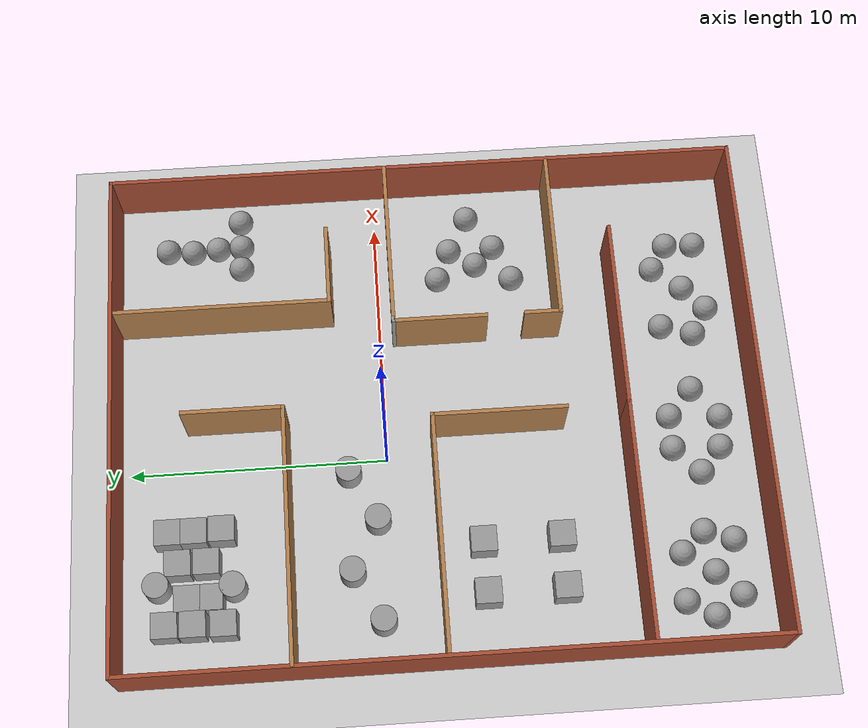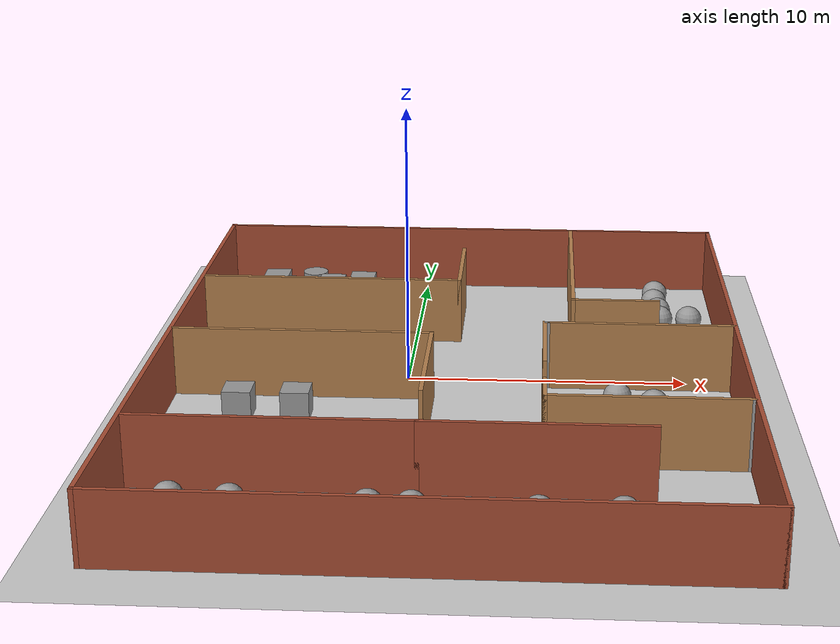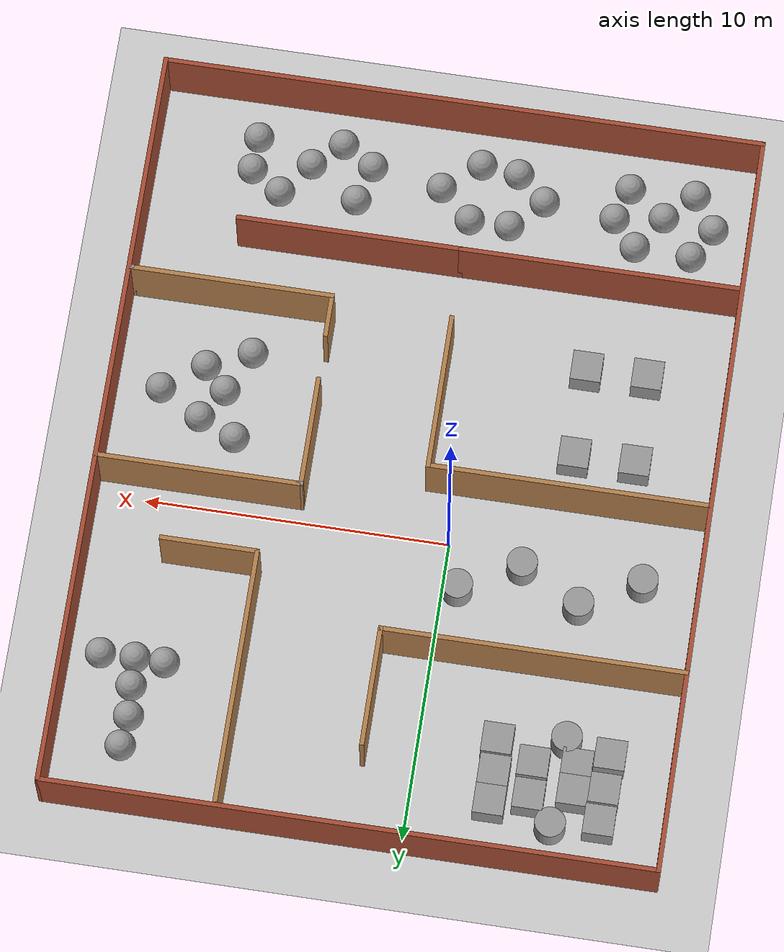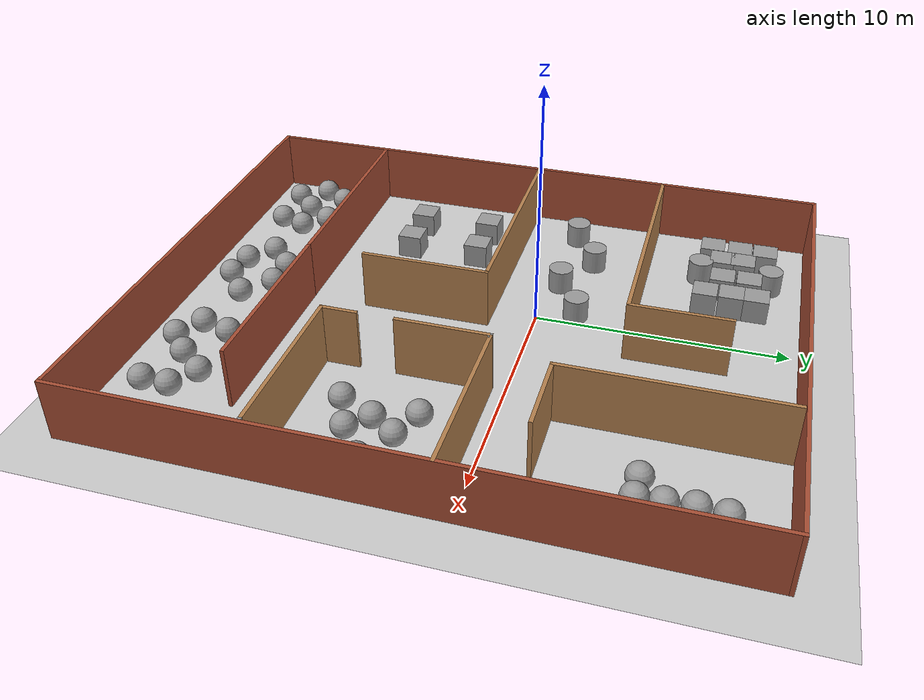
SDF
<sdf version="1.6">
 <world name="default">
  <light name="sun" type="directional">
   <pose>0 0 10 0 -0 0</pose>
   <diffuse>0.8 0.8 0.8 1</diffuse>
   <specular>0.2 0.2 0.2 1</specular>
   <attenuation>
    <range>1000</range>
    <constant>0.9</constant>
    <linear>0.01</linear>
    <quadratic>0.001</quadratic>
   </attenuation>
   <direction>-0.5 0.1 -0.9</direction>
  </light>
  <model name="ground_plane">
   <static>1</static>
   <link name="link">
    <collision name="collision">
     <geometry><plane><normal>0 0 1</normal><size>100 100</size></plane></geometry>
     <surface>
      <contact><collide_bitmask>65535</collide_bitmask></contact>
      <friction><ode><mu>100</mu><mu2>50</mu2></ode></friction>
     </surface>
    </collision>
    <visual name="visual">
     <cast_shadows>0</cast_shadows>
     <geometry><plane><normal>0 0 1</normal><size>100 100</size></plane></geometry>
     <material>
      <script><uri>file://media/materials/scripts/gazebo.material</uri><name>Gazebo/Grey</name></script>
     </material>
    </visual>
   </link>
  </model>
  <gravity>0 0 -9.8</gravity>
  <magnetic_field>6e-06 2.3e-05 -4.2e-05</magnetic_field>
  <atmosphere type="adiabatic"/>
  <physics name="default_physics" default="0" type="ode">
   <max_step_size>0.001</max_step_size>
   <real_time_factor>1</real_time_factor>
   <real_time_update_rate>1000</real_time_update_rate>
  </physics>
  <scene><ambient>0.4 0.4 0.4 1</ambient><background>0.7 0.7 0.7 1</background><shadows>1</shadows></scene>
  <audio><device>default</device></audio>
  <spherical_coordinates>
   <surface_model>EARTH_WGS84</surface_model>
   <latitude_deg>0</latitude_deg>
   <longitude_deg>0</longitude_deg>
   <elevation>0</elevation>
   <heading_deg>0</heading_deg>
  </spherical_coordinates>
  <model name="James_Condo">
   <pose>1.69249 -2.01582 0 0 -0 0</pose>
   <link name="Wall_0">
    <collision name="Wall_0_Collision">
     <geometry><box><size>25 0.15 2.5</size></box></geometry>
     <pose>0 0 1.25 0 -0 0</pose>
    </collision>
    <visual name="Wall_0_Visual">
     <pose>0 0 1.25 0 -0 0</pose>
     <geometry><box><size>25 0.15 2.5</size></box></geometry>
     <material>
      <script><uri>file://media/materials/scripts/gazebo.material</uri><name>Gazebo/Bricks</name></script>
      <ambient>1 1 1 1</ambient>
     </material>
     <meta><layer>0</layer></meta>
    </visual>
    <pose>-9.925 0 0 0 -0 1.5708</pose>
   </link>
   <link name="Wall_10">
    <collision name="Wall_10_Collision">
     <geometry><box><size>4 0.15 2.5</size></box></geometry>
     <pose>0 0 1.25 0 -0 0</pose>
    </collision>
    <visual name="Wall_10_Visual">
     <pose>0 0 1.25 0 -0 0</pose>
     <geometry><box><size>4 0.15 2.5</size></box></geometry>
     <material>
      <script><uri>file://media/materials/scripts/gazebo.material</uri><name>Gazebo/Wood</name></script>
      <ambient>1 1 1 1</ambient>
     </material>
     <meta><layer>0</layer></meta>
    </visual>
    <pose>-0.051792 7.79137 0 0 -0 1.5708</pose>
   </link>
   <link name="Wall_12">
    <collision name="Wall_12_Collision">
     <geometry><box><size>8.5 0.15 2.5</size></box></geometry>
     <pose>0 0 1.25 0 -0 0</pose>
    </collision>
    <visual name="Wall_12_Visual">
     <pose>0 0 1.25 0 -0 0</pose>
     <geometry><box><size>8.5 0.15 2.5</size></box></geometry>
     <material>
      <script><uri>file://media/materials/scripts/gazebo.material</uri><name>Gazebo/Wood</name></script>
      <ambient>1 1 1 1</ambient>
     </material>
     <meta><layer>0</layer></meta>
    </visual>
    <pose>4.24962 8.09027 0 0 -0 -1.5708</pose>
   </link>
   <link name="Wall_13">
    <collision name="Wall_13_Collision">
     <geometry><box><size>3.25 0.15 2.5</size></box></geometry>
     <pose>0 0 1.25 0 -0 0</pose>
    </collision>
    <visual name="Wall_13_Visual">
     <pose>0 0 1.25 0 -0 0</pose>
     <geometry><box><size>3.25 0.15 2.5</size></box></geometry>
     <material>
      <script><uri>file://media/materials/scripts/gazebo.material</uri><name>Gazebo/Wood</name></script>
      <ambient>1 1 1 1</ambient>
     </material>
     <meta><layer>0</layer></meta>
    </visual>
    <pose>5.79962 3.91527 0 0 -0 0</pose>
   </link>
   <link name="Wall_15">
    <collision name="Wall_15_Collision">
     <geometry><box><size>9.25 0.15 2.5</size></box></geometry>
     <pose>0 0 1.25 0 -0 0</pose>
    </collision>
    <visual name="Wall_15_Visual">
     <pose>0 0 1.25 0 -0 0</pose>
     <geometry><box><size>9.25 0.15 2.5</size></box></geometry>
     <material>
      <script><uri>file://media/materials/scripts/gazebo.material</uri><name>Gazebo/Wood</name></script>
      <ambient>1 1 1 1</ambient>
     </material>
     <meta><layer>0</layer></meta>
    </visual>
    <pose>-5.28144 0.205804 0 0 -0 0</pose>
   </link>
   <link name="Wall_18">
    <collision name="Wall_18_Collision">
     <geometry><box><size>9.25 0.15 2.5</size></box></geometry>
     <pose>0 0 1.25 0 -0 0</pose>
    </collision>
    <visual name="Wall_18_Visual">
     <pose>0 0 1.25 0 -0 0</pose>
     <geometry><box><size>9.25 0.15 2.5</size></box></geometry>
     <material>
      <script><uri>file://media/materials/scripts/gazebo.material</uri><name>Gazebo/Bricks</name></script>
      <ambient>1 1 1 1</ambient>
     </material>
     <meta><layer>0</layer></meta>
    </visual>
    <pose>-5.22874 -7.3006 0 0 -0 0</pose>
   </link>
   <link name="Wall_24">
    <collision name="Wall_24_Collision">
     <geometry><box><size>5.25 0.15 2.5</size></box></geometry>
     <pose>0 0 1.25 0 -0 0</pose>
    </collision>
    <visual name="Wall_24_Visual">
     <pose>0 0 1.25 0 -0 0</pose>
     <geometry><box><size>5.25 0.15 2.5</size></box></geometry>
     <material>
      <script><uri>file://media/materials/scripts/gazebo.material</uri><name>Gazebo/Wood</name></script>
      <ambient>1 1 1 1</ambient>
     </material>
     <meta><layer>0</layer></meta>
    </visual>
    <pose>-0.731434 -2.3442 0 0 -0 -1.5708</pose>
   </link>
   <link name="Wall_26">
    <collision name="Wall_26_Collision">
     <geometry><box><size>7.5 0.15 2.5</size></box></geometry>
     <pose>0 0 1.25 0 -0 0</pose>
    </collision>
    <visual name="Wall_26_Visual">
     <pose>0 0 1.25 0 -0 0</pose>
     <geometry><box><size>7.5 0.15 2.5</size></box></geometry>
     <material>
      <script><uri>file://media/materials/scripts/gazebo.material</uri><name>Gazebo/Bricks</name></script>
      <ambient>1 1 1 1</ambient>
     </material>
     <meta><layer>0</layer></meta>
    </visual>
    <pose>2.99626 -7.3006 0 0 -0 0</pose>
   </link>
   <link name="Wall_28">
    <collision name="Wall_28_Collision">
     <geometry><box><size>6.75 0.15 2.5</size></box></geometry>
     <pose>0 0 1.25 0 -0 0</pose>
    </collision>
    <visual name="Wall_28_Visual">
     <pose>0 0 1.25 0 -0 0</pose>
     <geometry><box><size>6.75 0.15 2.5</size></box></geometry>
     <material>
      <script><uri>file://media/materials/scripts/gazebo.material</uri><name>Gazebo/Wood</name></script>
      <ambient>1 1 1 1</ambient>
     </material>
     <meta><layer>0</layer></meta>
    </visual>
    <pose>6.62043 1.45525 0 0 -0 3.14159</pose>
   </link>
   <link name="Wall_29">
    <collision name="Wall_29_Collision">
     <geometry><box><size>0.25 0.15 2.5</size></box></geometry>
     <pose>0 0 1.25 0 -0 0</pose>
    </collision>
    <visual name="Wall_29_Visual">
     <pose>0 0 1.25 0 -0 0</pose>
     <geometry><box><size>0.25 0.15 2.5</size></box></geometry>
     <material>
      <script><uri>file://media/materials/scripts/gazebo.material</uri><name>Gazebo/Grey</name></script>
      <ambient>1 1 1 1</ambient>
     </material>
     <meta><layer>0</layer></meta>
    </visual>
    <pose>3.27043 1.45525 0 0 -0 3.14159</pose>
   </link>
   <link name="Wall_3">
    <collision name="Wall_3_Collision">
     <geometry><box><size>20 0.15 2.5</size></box></geometry>
     <pose>0 0 1.25 0 -0 0</pose>
    </collision>
    <visual name="Wall_3_Visual">
     <pose>0 0 1.25 0 -0 0</pose>
     <geometry><box><size>20 0.15 2.5</size></box></geometry>
     <material>
      <script><uri>file://media/materials/scripts/gazebo.material</uri><name>Gazebo/Bricks</name></script>
      <ambient>1 1 1 1</ambient>
     </material>
     <meta><layer>0</layer></meta>
    </visual>
    <pose>0 -12.425 0 0 -0 0</pose>
   </link>
   <link name="Wall_30">
    <collision name="Wall_30_Collision">
     <geometry><box><size>3.75 0.15 2.5</size></box></geometry>
     <pose>0 0 1.25 0 -0 0</pose>
    </collision>
    <visual name="Wall_30_Visual">
     <pose>0 0 1.25 0 -0 0</pose>
     <geometry><box><size>3.75 0.15 2.5</size></box></geometry>
     <material>
      <script><uri>file://media/materials/scripts/gazebo.material</uri><name>Gazebo/Wood</name></script>
      <ambient>1 1 1 1</ambient>
     </material>
     <meta><layer>0</layer></meta>
    </visual>
    <pose>3.22043 -0.344748 0 0 -0 -1.5708</pose>
   </link>
   <link name="Wall_32">
    <collision name="Wall_32_Collision">
     <geometry><box><size>1.5 0.15 2.5</size></box></geometry>
     <pose>0 0 1.25 0 -0 0</pose>
    </collision>
    <visual name="Wall_32_Visual">
     <pose>0 0 1.25 0 -0 0</pose>
     <geometry><box><size>1.5 0.15 2.5</size></box></geometry>
     <material>
      <script><uri>file://media/materials/scripts/gazebo.material</uri><name>Gazebo/Wood</name></script>
      <ambient>1 1 1 1</ambient>
     </material>
     <meta><layer>0</layer></meta>
    </visual>
    <pose>3.22858 -4.39072 0 0 -0 -1.5708</pose>
   </link>
   <link name="Wall_33">
    <collision name="Wall_33_Collision">
     <geometry><box><size>6.75 0.15 2.5</size></box></geometry>
     <pose>0 0 1.25 0 -0 0</pose>
    </collision>
    <visual name="Wall_33_Visual">
     <pose>0 0 1.25 0 -0 0</pose>
     <geometry><box><size>6.75 0.15 2.5</size></box></geometry>
     <material>
      <script><uri>file://media/materials/scripts/gazebo.material</uri><name>Gazebo/Wood</name></script>
      <ambient>1 1 1 1</ambient>
     </material>
     <meta><layer>0</layer></meta>
    </visual>
    <pose>6.52858 -5.06572 0 0 -0 0</pose>
   </link>
   <link name="Wall_34">
    <collision name="Wall_34_Collision">
     <geometry><box><size>0.15 0.15 2.5</size></box></geometry>
     <pose>0 0 1.25 0 -0 0</pose>
    </collision>
    <visual name="Wall_34_Visual">
     <pose>0 0 1.25 0 -0 0</pose>
     <geometry><box><size>0.15 0.15 2.5</size></box></geometry>
     <material>
      <script><uri>file://media/materials/scripts/gazebo.material</uri><name>Gazebo/Grey</name></script>
      <ambient>1 1 1 1</ambient>
     </material>
     <meta><layer>0</layer></meta>
    </visual>
    <pose>9.82858 -5.06572 0 0 -0 0</pose>
   </link>
   <link name="Wall_5">
    <collision name="Wall_5_Collision">
     <geometry><box><size>25 0.15 2.5</size></box></geometry>
     <pose>0 0 1.25 0 -0 0</pose>
    </collision>
    <visual name="Wall_5_Visual">
     <pose>0 0 1.25 0 -0 0</pose>
     <geometry><box><size>25 0.15 2.5</size></box></geometry>
     <material>
      <script><uri>file://media/materials/scripts/gazebo.material</uri><name>Gazebo/Bricks</name></script>
      <ambient>1 1 1 1</ambient>
     </material>
     <meta><layer>0</layer></meta>
    </visual>
    <pose>9.925 0 0 0 -0 1.5708</pose>
   </link>
   <link name="Wall_7">
    <collision name="Wall_7_Collision">
     <geometry><box><size>20 0.15 2.5</size></box></geometry>
     <pose>0 0 1.25 0 -0 0</pose>
    </collision>
    <visual name="Wall_7_Visual">
     <pose>0 0 1.25 0 -0 0</pose>
     <geometry><box><size>20 0.15 2.5</size></box></geometry>
     <material>
      <script><uri>file://media/materials/scripts/gazebo.material</uri><name>Gazebo/Bricks</name></script>
      <ambient>1 1 1 1</ambient>
     </material>
     <meta><layer>0</layer></meta>
    </visual>
    <pose>0 12.425 0 0 -0 0</pose>
   </link>
   <link name="Wall_9">
    <collision name="Wall_9_Collision">
     <geometry><box><size>10 0.15 2.5</size></box></geometry>
     <pose>0 0 1.25 0 -0 0</pose>
    </collision>
    <visual name="Wall_9_Visual">
     <pose>0 0 1.25 0 -0 0</pose>
     <geometry><box><size>10 0.15 2.5</size></box></geometry>
     <material>
      <script><uri>file://media/materials/scripts/gazebo.material</uri><name>Gazebo/Wood</name></script>
      <ambient>1 1 1 1</ambient>
     </material>
     <meta><layer>0</layer></meta>
    </visual>
    <pose>-4.97679 5.86637 0 0 -0 0</pose>
   </link>
   <static>1</static>
  </model>
  <model name="usedmap">
   <link name="link_1">
    <inertial>
     <mass>1</mass>
     <inertia>
      <ixx>0.166667</ixx>
      <ixy>0</ixy>
      <ixz>0</ixz>
      <iyy>0.166667</iyy>
      <iyz>0</iyz>
      <izz>0.166667</izz>
     </inertia>
    </inertial>
    <pose>-6.1695 -3.55407 0 0 -0 0</pose>
    <visual name="visual">
     <geometry><box><size>1 1 1</size></box></geometry>
     <material>
      <lighting>1</lighting>
      <script><uri>file://media/materials/scripts/gazebo.material</uri><name>Gazebo/Grey</name></script>
     </material>
    </visual>
    <collision name="collision">
     <geometry><box><size>1 1 1</size></box></geometry>
     <surface>
      <friction>
       <ode><mu>1</mu><mu2>1</mu2><fdir1>0 0 0</fdir1><slip1>0</slip1><slip2>0</slip2></ode>
       <torsional>
        <coefficient>1</coefficient>
        <patch_radius>0</patch_radius>
        <surface_radius>0</surface_radius>
        <use_patch_radius>1</use_patch_radius>
        <ode><slip>0</slip></ode>
       </torsional>
      </friction>
      <bounce><restitution_coefficient>0</restitution_coefficient><threshold>1e+06</threshold></bounce>
      <contact>
       <collide_without_contact>0</collide_without_contact>
       <collide_without_contact_bitmask>1</collide_without_contact_bitmask>
       <collide_bitmask>1</collide_bitmask>
       <ode>
        <soft_cfm>0</soft_cfm>
        <soft_erp>0.2</soft_erp>
        <kp>1e+13</kp>
        <kd>1</kd>
        <max_vel>0.01</max_vel>
        <min_depth>0</min_depth>
       </ode>
       <bullet>
        <split_impulse>1</split_impulse>
        <split_impulse_penetration_threshold>-0.01</split_impulse_penetration_threshold>
        <soft_cfm>0</soft_cfm>
        <soft_erp>0.2</soft_erp>
        <kp>1e+13</kp>
        <kd>1</kd>
       </bullet>
      </contact>
     </surface>
    </collision>
   </link>
   <link name="link_10">
    <inertial>
     <mass>1</mass>
     <inertia><ixx>0.1</ixx><ixy>0</ixy><ixz>0</ixz><iyy>0.1</iyy><iyz>0</iyz><izz>0.1</izz></inertia>
    </inertial>
    <pose>6.74143 -8.23001 0 0 -0 0</pose>
    <visual name="visual">
     <geometry><sphere><radius>0.5</radius></sphere></geometry>
     <material>
      <lighting>1</lighting>
      <script><uri>file://media/materials/scripts/gazebo.material</uri><name>Gazebo/Grey</name></script>
     </material>
    </visual>
    <collision name="collision">
     <geometry><sphere><radius>0.5</radius></sphere></geometry>
     <surface>
      <friction>
       <ode><mu>1</mu><mu2>1</mu2><fdir1>0 0 0</fdir1><slip1>0</slip1><slip2>0</slip2></ode>
       <torsional>
        <coefficient>1</coefficient>
        <patch_radius>0</patch_radius>
        <surface_radius>0</surface_radius>
        <use_patch_radius>1</use_patch_radius>
        <ode><slip>0</slip></ode>
       </torsional>
      </friction>
      <bounce><restitution_coefficient>0</restitution_coefficient><threshold>1e+06</threshold></bounce>
      <contact>
       <collide_without_contact>0</collide_without_contact>
       <collide_without_contact_bitmask>1</collide_without_contact_bitmask>
       <collide_bitmask>1</collide_bitmask>
       <ode>
        <soft_cfm>0</soft_cfm>
        <soft_erp>0.2</soft_erp>
        <kp>1e+13</kp>
        <kd>1</kd>
        <max_vel>0.01</max_vel>
        <min_depth>0</min_depth>
       </ode>
       <bullet>
        <split_impulse>1</split_impulse>
        <split_impulse_penetration_threshold>-0.01</split_impulse_penetration_threshold>
        <soft_cfm>0</soft_cfm>
        <soft_erp>0.2</soft_erp>
        <kp>1e+13</kp>
        <kd>1</kd>
       </bullet>
      </contact>
     </surface>
    </collision>
   </link>
   <link name="link_11">
    <inertial>
     <mass>1</mass>
     <inertia><ixx>0.1</ixx><ixy>0</ixy><ixz>0</ixz><iyy>0.1</iyy><iyz>0</iyz><izz>0.1</izz></inertia>
    </inertial>
    <pose>5.84403 -9.34728 0 0 -0 0</pose>
    <visual name="visual">
     <geometry><sphere><radius>0.5</radius></sphere></geometry>
     <material>
      <lighting>1</lighting>
      <script><uri>file://media/materials/scripts/gazebo.material</uri><name>Gazebo/Grey</name></script>
     </material>
    </visual>
    <collision name="collision">
     <geometry><sphere><radius>0.5</radius></sphere></geometry>
     <surface>
      <friction>
       <ode><mu>1</mu><mu2>1</mu2><fdir1>0 0 0</fdir1><slip1>0</slip1><slip2>0</slip2></ode>
       <torsional>
        <coefficient>1</coefficient>
        <patch_radius>0</patch_radius>
        <surface_radius>0</surface_radius>
        <use_patch_radius>1</use_patch_radius>
        <ode><slip>0</slip></ode>
       </torsional>
      </friction>
      <bounce><restitution_coefficient>0</restitution_coefficient><threshold>1e+06</threshold></bounce>
      <contact>
       <collide_without_contact>0</collide_without_contact>
       <collide_without_contact_bitmask>1</collide_without_contact_bitmask>
       <collide_bitmask>1</collide_bitmask>
       <ode>
        <soft_cfm>0</soft_cfm>
        <soft_erp>0.2</soft_erp>
        <kp>1e+13</kp>
        <kd>1</kd>
        <max_vel>0.01</max_vel>
        <min_depth>0</min_depth>
       </ode>
       <bullet>
        <split_impulse>1</split_impulse>
        <split_impulse_penetration_threshold>-0.01</split_impulse_penetration_threshold>
        <soft_cfm>0</soft_cfm>
        <soft_erp>0.2</soft_erp>
        <kp>1e+13</kp>
        <kd>1</kd>
       </bullet>
      </contact>
     </surface>
    </collision>
   </link>
   <link name="link_12">
    <inertial>
     <mass>1</mass>
     <inertia><ixx>0.1</ixx><ixy>0</ixy><ixz>0</ixz><iyy>0.1</iyy><iyz>0</iyz><izz>0.1</izz></inertia>
    </inertial>
    <pose>4.90267 -10.1971 0 0 -0 0</pose>
    <visual name="visual">
     <geometry><sphere><radius>0.5</radius></sphere></geometry>
     <material>
      <lighting>1</lighting>
      <script><uri>file://media/materials/scripts/gazebo.material</uri><name>Gazebo/Grey</name></script>
     </material>
    </visual>
    <collision name="collision">
     <geometry><sphere><radius>0.5</radius></sphere></geometry>
     <surface>
      <friction>
       <ode><mu>1</mu><mu2>1</mu2><fdir1>0 0 0</fdir1><slip1>0</slip1><slip2>0</slip2></ode>
       <torsional>
        <coefficient>1</coefficient>
        <patch_radius>0</patch_radius>
        <surface_radius>0</surface_radius>
        <use_patch_radius>1</use_patch_radius>
        <ode><slip>0</slip></ode>
       </torsional>
      </friction>
      <bounce><restitution_coefficient>0</restitution_coefficient><threshold>1e+06</threshold></bounce>
      <contact>
       <collide_without_contact>0</collide_without_contact>
       <collide_without_contact_bitmask>1</collide_without_contact_bitmask>
       <collide_bitmask>1</collide_bitmask>
       <ode>
        <soft_cfm>0</soft_cfm>
        <soft_erp>0.2</soft_erp>
        <kp>1e+13</kp>
        <kd>1</kd>
        <max_vel>0.01</max_vel>
        <min_depth>0</min_depth>
       </ode>
       <bullet>
        <split_impulse>1</split_impulse>
        <split_impulse_penetration_threshold>-0.01</split_impulse_penetration_threshold>
        <soft_cfm>0</soft_cfm>
        <soft_erp>0.2</soft_erp>
        <kp>1e+13</kp>
        <kd>1</kd>
       </bullet>
      </contact>
     </surface>
    </collision>
   </link>
   <link name="link_13">
    <inertial>
     <mass>1</mass>
     <inertia><ixx>0.1</ixx><ixy>0</ixy><ixz>0</ixz><iyy>0.1</iyy><iyz>0</iyz><izz>0.1</izz></inertia>
    </inertial>
    <pose>3.83526 -9.56031 0 0 -0 0</pose>
    <visual name="visual">
     <geometry><sphere><radius>0.5</radius></sphere></geometry>
     <material>
      <lighting>1</lighting>
      <script><uri>file://media/materials/scripts/gazebo.material</uri><name>Gazebo/Grey</name></script>
     </material>
    </visual>
    <collision name="collision">
     <geometry><sphere><radius>0.5</radius></sphere></geometry>
     <surface>
      <friction>
       <ode><mu>1</mu><mu2>1</mu2><fdir1>0 0 0</fdir1><slip1>0</slip1><slip2>0</slip2></ode>
       <torsional>
        <coefficient>1</coefficient>
        <patch_radius>0</patch_radius>
        <surface_radius>0</surface_radius>
        <use_patch_radius>1</use_patch_radius>
        <ode><slip>0</slip></ode>
       </torsional>
      </friction>
      <bounce><restitution_coefficient>0</restitution_coefficient><threshold>1e+06</threshold></bounce>
      <contact>
       <collide_without_contact>0</collide_without_contact>
       <collide_without_contact_bitmask>1</collide_without_contact_bitmask>
       <collide_bitmask>1</collide_bitmask>
       <ode>
        <soft_cfm>0</soft_cfm>
        <soft_erp>0.2</soft_erp>
        <kp>1e+13</kp>
        <kd>1</kd>
        <max_vel>0.01</max_vel>
        <min_depth>0</min_depth>
       </ode>
       <bullet>
        <split_impulse>1</split_impulse>
        <split_impulse_penetration_threshold>-0.01</split_impulse_penetration_threshold>
        <soft_cfm>0</soft_cfm>
        <soft_erp>0.2</soft_erp>
        <kp>1e+13</kp>
        <kd>1</kd>
       </bullet>
      </contact>
     </surface>
    </collision>
   </link>
   <link name="link_14">
    <inertial>
     <mass>1</mass>
     <inertia><ixx>0.1</ixx><ixy>0</ixy><ixz>0</ixz><iyy>0.1</iyy><iyz>0</iyz><izz>0.1</izz></inertia>
    </inertial>
    <pose>4.20738 -8.31328 0 0 -0 0</pose>
    <visual name="visual">
     <geometry><sphere><radius>0.5</radius></sphere></geometry>
     <material>
      <lighting>1</lighting>
      <script><uri>file://media/materials/scripts/gazebo.material</uri><name>Gazebo/Grey</name></script>
     </material>
    </visual>
    <collision name="collision">
     <geometry><sphere><radius>0.5</radius></sphere></geometry>
     <surface>
      <friction>
       <ode><mu>1</mu><mu2>1</mu2><fdir1>0 0 0</fdir1><slip1>0</slip1><slip2>0</slip2></ode>
       <torsional>
        <coefficient>1</coefficient>
        <patch_radius>0</patch_radius>
        <surface_radius>0</surface_radius>
        <use_patch_radius>1</use_patch_radius>
        <ode><slip>0</slip></ode>
       </torsional>
      </friction>
      <bounce><restitution_coefficient>0</restitution_coefficient><threshold>1e+06</threshold></bounce>
      <contact>
       <collide_without_contact>0</collide_without_contact>
       <collide_without_contact_bitmask>1</collide_without_contact_bitmask>
       <collide_bitmask>1</collide_bitmask>
       <ode>
        <soft_cfm>0</soft_cfm>
        <soft_erp>0.2</soft_erp>
        <kp>1e+13</kp>
        <kd>1</kd>
        <max_vel>0.01</max_vel>
        <min_depth>0</min_depth>
       </ode>
       <bullet>
        <split_impulse>1</split_impulse>
        <split_impulse_penetration_threshold>-0.01</split_impulse_penetration_threshold>
        <soft_cfm>0</soft_cfm>
        <soft_erp>0.2</soft_erp>
        <kp>1e+13</kp>
        <kd>1</kd>
       </bullet>
      </contact>
     </surface>
    </collision>
   </link>
   <link name="link_15">
    <inertial>
     <mass>1</mass>
     <inertia><ixx>0.1</ixx><ixy>0</ixy><ixz>0</ixz><iyy>0.1</iyy><iyz>0</iyz><izz>0.1</izz></inertia>
    </inertial>
    <pose>1.47707 -9.16716 0 0 -0 0</pose>
    <visual name="visual">
     <geometry><sphere><radius>0.5</radius></sphere></geometry>
     <material>
      <lighting>1</lighting>
      <script><uri>file://media/materials/scripts/gazebo.material</uri><name>Gazebo/Grey</name></script>
     </material>
    </visual>
    <collision name="collision">
     <geometry><sphere><radius>0.5</radius></sphere></geometry>
     <surface>
      <friction>
       <ode><mu>1</mu><mu2>1</mu2><fdir1>0 0 0</fdir1><slip1>0</slip1><slip2>0</slip2></ode>
       <torsional>
        <coefficient>1</coefficient>
        <patch_radius>0</patch_radius>
        <surface_radius>0</surface_radius>
        <use_patch_radius>1</use_patch_radius>
        <ode><slip>0</slip></ode>
       </torsional>
      </friction>
      <bounce><restitution_coefficient>0</restitution_coefficient><threshold>1e+06</threshold></bounce>
      <contact>
       <collide_without_contact>0</collide_without_contact>
       <collide_without_contact_bitmask>1</collide_without_contact_bitmask>
       <collide_bitmask>1</collide_bitmask>
       <ode>
        <soft_cfm>0</soft_cfm>
        <soft_erp>0.2</soft_erp>
        <kp>1e+13</kp>
        <kd>1</kd>
        <max_vel>0.01</max_vel>
        <min_depth>0</min_depth>
       </ode>
       <bullet>
        <split_impulse>1</split_impulse>
        <split_impulse_penetration_threshold>-0.01</split_impulse_penetration_threshold>
        <soft_cfm>0</soft_cfm>
        <soft_erp>0.2</soft_erp>
        <kp>1e+13</kp>
        <kd>1</kd>
       </bullet>
      </contact>
     </surface>
    </collision>
   </link>
   <link name="link_16">
    <inertial>
     <mass>1</mass>
     <inertia><ixx>0.1</ixx><ixy>0</ixy><ixz>0</ixz><iyy>0.1</iyy><iyz>0</iyz><izz>0.1</izz></inertia>
    </inertial>
    <pose>0.394526 -8.1918 0 0 -0 0</pose>
    <visual name="visual">
     <geometry><sphere><radius>0.5</radius></sphere></geometry>
     <material>
      <lighting>1</lighting>
      <script><uri>file://media/materials/scripts/gazebo.material</uri><name>Gazebo/Grey</name></script>
     </material>
    </visual>
    <collision name="collision">
     <geometry><sphere><radius>0.5</radius></sphere></geometry>
     <surface>
      <friction>
       <ode><mu>1</mu><mu2>1</mu2><fdir1>0 0 0</fdir1><slip1>0</slip1><slip2>0</slip2></ode>
       <torsional>
        <coefficient>1</coefficient>
        <patch_radius>0</patch_radius>
        <surface_radius>0</surface_radius>
        <use_patch_radius>1</use_patch_radius>
        <ode><slip>0</slip></ode>
       </torsional>
      </friction>
      <bounce><restitution_coefficient>0</restitution_coefficient><threshold>1e+06</threshold></bounce>
      <contact>
       <collide_without_contact>0</collide_without_contact>
       <collide_without_contact_bitmask>1</collide_without_contact_bitmask>
       <collide_bitmask>1</collide_bitmask>
       <ode>
        <soft_cfm>0</soft_cfm>
        <soft_erp>0.2</soft_erp>
        <kp>1e+13</kp>
        <kd>1</kd>
        <max_vel>0.01</max_vel>
        <min_depth>0</min_depth>
       </ode>
       <bullet>
        <split_impulse>1</split_impulse>
        <split_impulse_penetration_threshold>-0.01</split_impulse_penetration_threshold>
        <soft_cfm>0</soft_cfm>
        <soft_erp>0.2</soft_erp>
        <kp>1e+13</kp>
        <kd>1</kd>
       </bullet>
      </contact>
     </surface>
    </collision>
   </link>
   <link name="link_17">
    <inertial>
     <mass>1</mass>
     <inertia><ixx>0.1</ixx><ixy>0</ixy><ixz>0</ixz><iyy>0.1</iyy><iyz>0</iyz><izz>0.1</izz></inertia>
    </inertial>
    <pose>0.267932 -10.1678 0 0 -0 0</pose>
    <visual name="visual">
     <geometry><sphere><radius>0.5</radius></sphere></geometry>
     <material>
      <lighting>1</lighting>
      <script><uri>file://media/materials/scripts/gazebo.material</uri><name>Gazebo/Grey</name></script>
     </material>
    </visual>
    <collision name="collision">
     <geometry><sphere><radius>0.5</radius></sphere></geometry>
     <surface>
      <friction>
       <ode><mu>1</mu><mu2>1</mu2><fdir1>0 0 0</fdir1><slip1>0</slip1><slip2>0</slip2></ode>
       <torsional>
        <coefficient>1</coefficient>
        <patch_radius>0</patch_radius>
        <surface_radius>0</surface_radius>
        <use_patch_radius>1</use_patch_radius>
        <ode><slip>0</slip></ode>
       </torsional>
      </friction>
      <bounce><restitution_coefficient>0</restitution_coefficient><threshold>1e+06</threshold></bounce>
      <contact>
       <collide_without_contact>0</collide_without_contact>
       <collide_without_contact_bitmask>1</collide_without_contact_bitmask>
       <collide_bitmask>1</collide_bitmask>
       <ode>
        <soft_cfm>0</soft_cfm>
        <soft_erp>0.2</soft_erp>
        <kp>1e+13</kp>
        <kd>1</kd>
        <max_vel>0.01</max_vel>
        <min_depth>0</min_depth>
       </ode>
       <bullet>
        <split_impulse>1</split_impulse>
        <split_impulse_penetration_threshold>-0.01</split_impulse_penetration_threshold>
        <soft_cfm>0</soft_cfm>
        <soft_erp>0.2</soft_erp>
        <kp>1e+13</kp>
        <kd>1</kd>
       </bullet>
      </contact>
     </surface>
    </collision>
   </link>
   <link name="link_2">
    <inertial>
     <mass>1</mass>
     <inertia>
      <ixx>0.166667</ixx>
      <ixy>0</ixy>
      <ixz>0</ixz>
      <iyy>0.166667</iyy>
      <iyz>0</iyz>
      <izz>0.166667</izz>
     </inertia>
    </inertial>
    <pose>-6.1883 -0.561039 0 0 -0 0</pose>
    <visual name="visual">
     <geometry><box><size>1 1 1</size></box></geometry>
     <material>
      <lighting>1</lighting>
      <script><uri>file://media/materials/scripts/gazebo.material</uri><name>Gazebo/Grey</name></script>
     </material>
    </visual>
    <collision name="collision">
     <geometry><box><size>1 1 1</size></box></geometry>
     <surface>
      <friction>
       <ode><mu>1</mu><mu2>1</mu2><fdir1>0 0 0</fdir1><slip1>0</slip1><slip2>0</slip2></ode>
       <torsional>
        <coefficient>1</coefficient>
        <patch_radius>0</patch_radius>
        <surface_radius>0</surface_radius>
        <use_patch_radius>1</use_patch_radius>
        <ode><slip>0</slip></ode>
       </torsional>
      </friction>
      <bounce><restitution_coefficient>0</restitution_coefficient><threshold>1e+06</threshold></bounce>
      <contact>
       <collide_without_contact>0</collide_without_contact>
       <collide_without_contact_bitmask>1</collide_without_contact_bitmask>
       <collide_bitmask>1</collide_bitmask>
       <ode>
        <soft_cfm>0</soft_cfm>
        <soft_erp>0.2</soft_erp>
        <kp>1e+13</kp>
        <kd>1</kd>
        <max_vel>0.01</max_vel>
        <min_depth>0</min_depth>
       </ode>
       <bullet>
        <split_impulse>1</split_impulse>
        <split_impulse_penetration_threshold>-0.01</split_impulse_penetration_threshold>
        <soft_cfm>0</soft_cfm>
        <soft_erp>0.2</soft_erp>
        <kp>1e+13</kp>
        <kd>1</kd>
       </bullet>
      </contact>
     </surface>
    </collision>
   </link>
   <link name="link_20">
    <inertial>
     <mass>1</mass>
     <inertia><ixx>0.1</ixx><ixy>0</ixy><ixz>0</ixz><iyy>0.1</iyy><iyz>0</iyz><izz>0.1</izz></inertia>
    </inertial>
    <pose>-0.984284 -10.0243 0 0 -0 0</pose>
    <visual name="visual">
     <geometry><sphere><radius>0.5</radius></sphere></geometry>
     <material>
      <lighting>1</lighting>
      <script><uri>file://media/materials/scripts/gazebo.material</uri><name>Gazebo/Grey</name></script>
     </material>
    </visual>
    <collision name="collision">
     <geometry><sphere><radius>0.5</radius></sphere></geometry>
     <surface>
      <friction>
       <ode><mu>1</mu><mu2>1</mu2><fdir1>0 0 0</fdir1><slip1>0</slip1><slip2>0</slip2></ode>
       <torsional>
        <coefficient>1</coefficient>
        <patch_radius>0</patch_radius>
        <surface_radius>0</surface_radius>
        <use_patch_radius>1</use_patch_radius>
        <ode><slip>0</slip></ode>
       </torsional>
      </friction>
      <bounce><restitution_coefficient>0</restitution_coefficient><threshold>1e+06</threshold></bounce>
      <contact>
       <collide_without_contact>0</collide_without_contact>
       <collide_without_contact_bitmask>1</collide_without_contact_bitmask>
       <collide_bitmask>1</collide_bitmask>
       <ode>
        <soft_cfm>0</soft_cfm>
        <soft_erp>0.2</soft_erp>
        <kp>1e+13</kp>
        <kd>1</kd>
        <max_vel>0.01</max_vel>
        <min_depth>0</min_depth>
       </ode>
       <bullet>
        <split_impulse>1</split_impulse>
        <split_impulse_penetration_threshold>-0.01</split_impulse_penetration_threshold>
        <soft_cfm>0</soft_cfm>
        <soft_erp>0.2</soft_erp>
        <kp>1e+13</kp>
        <kd>1</kd>
       </bullet>
      </contact>
     </surface>
    </collision>
   </link>
   <link name="link_21">
    <inertial>
     <mass>1</mass>
     <inertia><ixx>0.1</ixx><ixy>0</ixy><ixz>0</ixz><iyy>0.1</iyy><iyz>0</iyz><izz>0.1</izz></inertia>
    </inertial>
    <pose>-1.96242 -9.18554 0 0 -0 0</pose>
    <visual name="visual">
     <geometry><sphere><radius>0.5</radius></sphere></geometry>
     <material>
      <lighting>1</lighting>
      <script><uri>file://media/materials/scripts/gazebo.material</uri><name>Gazebo/Grey</name></script>
     </material>
    </visual>
    <collision name="collision">
     <geometry><sphere><radius>0.5</radius></sphere></geometry>
     <surface>
      <friction>
       <ode><mu>1</mu><mu2>1</mu2><fdir1>0 0 0</fdir1><slip1>0</slip1><slip2>0</slip2></ode>
       <torsional>
        <coefficient>1</coefficient>
        <patch_radius>0</patch_radius>
        <surface_radius>0</surface_radius>
        <use_patch_radius>1</use_patch_radius>
        <ode><slip>0</slip></ode>
       </torsional>
      </friction>
      <bounce><restitution_coefficient>0</restitution_coefficient><threshold>1e+06</threshold></bounce>
      <contact>
       <collide_without_contact>0</collide_without_contact>
       <collide_without_contact_bitmask>1</collide_without_contact_bitmask>
       <collide_bitmask>1</collide_bitmask>
       <ode>
        <soft_cfm>0</soft_cfm>
        <soft_erp>0.2</soft_erp>
        <kp>1e+13</kp>
        <kd>1</kd>
        <max_vel>0.01</max_vel>
        <min_depth>0</min_depth>
       </ode>
       <bullet>
        <split_impulse>1</split_impulse>
        <split_impulse_penetration_threshold>-0.01</split_impulse_penetration_threshold>
        <soft_cfm>0</soft_cfm>
        <soft_erp>0.2</soft_erp>
        <kp>1e+13</kp>
        <kd>1</kd>
       </bullet>
      </contact>
     </surface>
    </collision>
   </link>
   <link name="link_22">
    <inertial>
     <mass>1</mass>
     <inertia><ixx>0.1</ixx><ixy>0</ixy><ixz>0</ixz><iyy>0.1</iyy><iyz>0</iyz><izz>0.1</izz></inertia>
    </inertial>
    <pose>-0.927433 -8.17566 0 0 -0 0</pose>
    <visual name="visual">
     <geometry><sphere><radius>0.5</radius></sphere></geometry>
     <material>
      <lighting>1</lighting>
      <script><uri>file://media/materials/scripts/gazebo.material</uri><name>Gazebo/Grey</name></script>
     </material>
    </visual>
    <collision name="collision">
     <geometry><sphere><radius>0.5</radius></sphere></geometry>
     <surface>
      <friction>
       <ode><mu>1</mu><mu2>1</mu2><fdir1>0 0 0</fdir1><slip1>0</slip1><slip2>0</slip2></ode>
       <torsional>
        <coefficient>1</coefficient>
        <patch_radius>0</patch_radius>
        <surface_radius>0</surface_radius>
        <use_patch_radius>1</use_patch_radius>
        <ode><slip>0</slip></ode>
       </torsional>
      </friction>
      <bounce><restitution_coefficient>0</restitution_coefficient><threshold>1e+06</threshold></bounce>
      <contact>
       <collide_without_contact>0</collide_without_contact>
       <collide_without_contact_bitmask>1</collide_without_contact_bitmask>
       <collide_bitmask>1</collide_bitmask>
       <ode>
        <soft_cfm>0</soft_cfm>
        <soft_erp>0.2</soft_erp>
        <kp>1e+13</kp>
        <kd>1</kd>
        <max_vel>0.01</max_vel>
        <min_depth>0</min_depth>
       </ode>
       <bullet>
        <split_impulse>1</split_impulse>
        <split_impulse_penetration_threshold>-0.01</split_impulse_penetration_threshold>
        <soft_cfm>0</soft_cfm>
        <soft_erp>0.2</soft_erp>
        <kp>1e+13</kp>
        <kd>1</kd>
       </bullet>
      </contact>
     </surface>
    </collision>
   </link>
   <link name="link_23">
    <inertial>
     <mass>1</mass>
     <inertia><ixx>0.1</ixx><ixy>0</ixy><ixz>0</ixz><iyy>0.1</iyy><iyz>0</iyz><izz>0.1</izz></inertia>
    </inertial>
    <pose>-4.32819 -8.95262 0 0 -0 0</pose>
    <visual name="visual">
     <geometry><sphere><radius>0.5</radius></sphere></geometry>
     <material>
      <lighting>1</lighting>
      <script><uri>file://media/materials/scripts/gazebo.material</uri><name>Gazebo/Grey</name></script>
     </material>
    </visual>
    <collision name="collision">
     <geometry><sphere><radius>0.5</radius></sphere></geometry>
     <surface>
      <friction>
       <ode><mu>1</mu><mu2>1</mu2><fdir1>0 0 0</fdir1><slip1>0</slip1><slip2>0</slip2></ode>
       <torsional>
        <coefficient>1</coefficient>
        <patch_radius>0</patch_radius>
        <surface_radius>0</surface_radius>
        <use_patch_radius>1</use_patch_radius>
        <ode><slip>0</slip></ode>
       </torsional>
      </friction>
      <bounce><restitution_coefficient>0</restitution_coefficient><threshold>1e+06</threshold></bounce>
      <contact>
       <collide_without_contact>0</collide_without_contact>
       <collide_without_contact_bitmask>1</collide_without_contact_bitmask>
       <collide_bitmask>1</collide_bitmask>
       <ode>
        <soft_cfm>0</soft_cfm>
        <soft_erp>0.2</soft_erp>
        <kp>1e+13</kp>
        <kd>1</kd>
        <max_vel>0.01</max_vel>
        <min_depth>0</min_depth>
       </ode>
       <bullet>
        <split_impulse>1</split_impulse>
        <split_impulse_penetration_threshold>-0.01</split_impulse_penetration_threshold>
        <soft_cfm>0</soft_cfm>
        <soft_erp>0.2</soft_erp>
        <kp>1e+13</kp>
        <kd>1</kd>
       </bullet>
      </contact>
     </surface>
    </collision>
   </link>
   <link name="link_24">
    <inertial>
     <mass>1</mass>
     <inertia><ixx>0.1</ixx><ixy>0</ixy><ixz>0</ixz><iyy>0.1</iyy><iyz>0</iyz><izz>0.1</izz></inertia>
    </inertial>
    <pose>-4.70582 -10.0665 0 0 -0 0</pose>
    <visual name="visual">
     <geometry><sphere><radius>0.5</radius></sphere></geometry>
     <material>
      <lighting>1</lighting>
      <script><uri>file://media/materials/scripts/gazebo.material</uri><name>Gazebo/Grey</name></script>
     </material>
    </visual>
    <collision name="collision">
     <geometry><sphere><radius>0.5</radius></sphere></geometry>
     <surface>
      <friction>
       <ode><mu>1</mu><mu2>1</mu2><fdir1>0 0 0</fdir1><slip1>0</slip1><slip2>0</slip2></ode>
       <torsional>
        <coefficient>1</coefficient>
        <patch_radius>0</patch_radius>
        <surface_radius>0</surface_radius>
        <use_patch_radius>1</use_patch_radius>
        <ode><slip>0</slip></ode>
       </torsional>
      </friction>
      <bounce><restitution_coefficient>0</restitution_coefficient><threshold>1e+06</threshold></bounce>
      <contact>
       <collide_without_contact>0</collide_without_contact>
       <collide_without_contact_bitmask>1</collide_without_contact_bitmask>
       <collide_bitmask>1</collide_bitmask>
       <ode>
        <soft_cfm>0</soft_cfm>
        <soft_erp>0.2</soft_erp>
        <kp>1e+13</kp>
        <kd>1</kd>
        <max_vel>0.01</max_vel>
        <min_depth>0</min_depth>
       </ode>
       <bullet>
        <split_impulse>1</split_impulse>
        <split_impulse_penetration_threshold>-0.01</split_impulse_penetration_threshold>
        <soft_cfm>0</soft_cfm>
        <soft_erp>0.2</soft_erp>
        <kp>1e+13</kp>
        <kd>1</kd>
       </bullet>
      </contact>
     </surface>
    </collision>
   </link>
   <link name="link_25">
    <inertial>
     <mass>1</mass>
     <inertia><ixx>0.1</ixx><ixy>0</ixy><ixz>0</ixz><iyy>0.1</iyy><iyz>0</iyz><izz>0.1</izz></inertia>
    </inertial>
    <pose>-5.12604 -8.04998 0 0 -0 0</pose>
    <visual name="visual">
     <geometry><sphere><radius>0.5</radius></sphere></geometry>
     <material>
      <lighting>1</lighting>
      <script><uri>file://media/materials/scripts/gazebo.material</uri><name>Gazebo/Grey</name></script>
     </material>
    </visual>
    <collision name="collision">
     <geometry><sphere><radius>0.5</radius></sphere></geometry>
     <surface>
      <friction>
       <ode><mu>1</mu><mu2>1</mu2><fdir1>0 0 0</fdir1><slip1>0</slip1><slip2>0</slip2></ode>
       <torsional>
        <coefficient>1</coefficient>
        <patch_radius>0</patch_radius>
        <surface_radius>0</surface_radius>
        <use_patch_radius>1</use_patch_radius>
        <ode><slip>0</slip></ode>
       </torsional>
      </friction>
      <bounce><restitution_coefficient>0</restitution_coefficient><threshold>1e+06</threshold></bounce>
      <contact>
       <collide_without_contact>0</collide_without_contact>
       <collide_without_contact_bitmask>1</collide_without_contact_bitmask>
       <collide_bitmask>1</collide_bitmask>
       <ode>
        <soft_cfm>0</soft_cfm>
        <soft_erp>0.2</soft_erp>
        <kp>1e+13</kp>
        <kd>1</kd>
        <max_vel>0.01</max_vel>
        <min_depth>0</min_depth>
       </ode>
       <bullet>
        <split_impulse>1</split_impulse>
        <split_impulse_penetration_threshold>-0.01</split_impulse_penetration_threshold>
        <soft_cfm>0</soft_cfm>
        <soft_erp>0.2</soft_erp>
        <kp>1e+13</kp>
        <kd>1</kd>
       </bullet>
      </contact>
     </surface>
    </collision>
   </link>
   <link name="link_26">
    <inertial>
     <mass>1</mass>
     <inertia><ixx>0.1</ixx><ixy>0</ixy><ixz>0</ixz><iyy>0.1</iyy><iyz>0</iyz><izz>0.1</izz></inertia>
    </inertial>
    <pose>-5.92984 -9.21674 0 0 -0 0</pose>
    <visual name="visual">
     <geometry><sphere><radius>0.5</radius></sphere></geometry>
     <material>
      <lighting>1</lighting>
      <script><uri>file://media/materials/scripts/gazebo.material</uri><name>Gazebo/Grey</name></script>
     </material>
    </visual>
    <collision name="collision">
     <geometry><sphere><radius>0.5</radius></sphere></geometry>
     <surface>
      <friction>
       <ode><mu>1</mu><mu2>1</mu2><fdir1>0 0 0</fdir1><slip1>0</slip1><slip2>0</slip2></ode>
       <torsional>
        <coefficient>1</coefficient>
        <patch_radius>0</patch_radius>
        <surface_radius>0</surface_radius>
        <use_patch_radius>1</use_patch_radius>
        <ode><slip>0</slip></ode>
       </torsional>
      </friction>
      <bounce><restitution_coefficient>0</restitution_coefficient><threshold>1e+06</threshold></bounce>
      <contact>
       <collide_without_contact>0</collide_without_contact>
       <collide_without_contact_bitmask>1</collide_without_contact_bitmask>
       <collide_bitmask>1</collide_bitmask>
       <ode>
        <soft_cfm>0</soft_cfm>
        <soft_erp>0.2</soft_erp>
        <kp>1e+13</kp>
        <kd>1</kd>
        <max_vel>0.01</max_vel>
        <min_depth>0</min_depth>
       </ode>
       <bullet>
        <split_impulse>1</split_impulse>
        <split_impulse_penetration_threshold>-0.01</split_impulse_penetration_threshold>
        <soft_cfm>0</soft_cfm>
        <soft_erp>0.2</soft_erp>
        <kp>1e+13</kp>
        <kd>1</kd>
       </bullet>
      </contact>
     </surface>
    </collision>
   </link>
   <link name="link_27">
    <inertial>
     <mass>1</mass>
     <inertia><ixx>0.1</ixx><ixy>0</ixy><ixz>0</ixz><iyy>0.1</iyy><iyz>0</iyz><izz>0.1</izz></inertia>
    </inertial>
    <pose>-6.86562 -10.1499 0 0 -0 0</pose>
    <visual name="visual">
     <geometry><sphere><radius>0.5</radius></sphere></geometry>
     <material>
      <lighting>1</lighting>
      <script><uri>file://media/materials/scripts/gazebo.material</uri><name>Gazebo/Grey</name></script>
     </material>
    </visual>
    <collision name="collision">
     <geometry><sphere><radius>0.5</radius></sphere></geometry>
     <surface>
      <friction>
       <ode><mu>1</mu><mu2>1</mu2><fdir1>0 0 0</fdir1><slip1>0</slip1><slip2>0</slip2></ode>
       <torsional>
        <coefficient>1</coefficient>
        <patch_radius>0</patch_radius>
        <surface_radius>0</surface_radius>
        <use_patch_radius>1</use_patch_radius>
        <ode><slip>0</slip></ode>
       </torsional>
      </friction>
      <bounce><restitution_coefficient>0</restitution_coefficient><threshold>1e+06</threshold></bounce>
      <contact>
       <collide_without_contact>0</collide_without_contact>
       <collide_without_contact_bitmask>1</collide_without_contact_bitmask>
       <collide_bitmask>1</collide_bitmask>
       <ode>
        <soft_cfm>0</soft_cfm>
        <soft_erp>0.2</soft_erp>
        <kp>1e+13</kp>
        <kd>1</kd>
        <max_vel>0.01</max_vel>
        <min_depth>0</min_depth>
       </ode>
       <bullet>
        <split_impulse>1</split_impulse>
        <split_impulse_penetration_threshold>-0.01</split_impulse_penetration_threshold>
        <soft_cfm>0</soft_cfm>
        <soft_erp>0.2</soft_erp>
        <kp>1e+13</kp>
        <kd>1</kd>
       </bullet>
      </contact>
     </surface>
    </collision>
   </link>
   <link name="link_28">
    <inertial>
     <mass>1</mass>
     <inertia><ixx>0.1</ixx><ixy>0</ixy><ixz>0</ixz><iyy>0.1</iyy><iyz>0</iyz><izz>0.1</izz></inertia>
    </inertial>
    <pose>-7.60502 -9.04078 0 0 -0 0</pose>
    <visual name="visual">
     <geometry><sphere><radius>0.5</radius></sphere></geometry>
     <material>
      <lighting>1</lighting>
      <script><uri>file://media/materials/scripts/gazebo.material</uri><name>Gazebo/Grey</name></script>
     </material>
    </visual>
    <collision name="collision">
     <geometry><sphere><radius>0.5</radius></sphere></geometry>
     <surface>
      <friction>
       <ode><mu>1</mu><mu2>1</mu2><fdir1>0 0 0</fdir1><slip1>0</slip1><slip2>0</slip2></ode>
       <torsional>
        <coefficient>1</coefficient>
        <patch_radius>0</patch_radius>
        <surface_radius>0</surface_radius>
        <use_patch_radius>1</use_patch_radius>
        <ode><slip>0</slip></ode>
       </torsional>
      </friction>
      <bounce><restitution_coefficient>0</restitution_coefficient><threshold>1e+06</threshold></bounce>
      <contact>
       <collide_without_contact>0</collide_without_contact>
       <collide_without_contact_bitmask>1</collide_without_contact_bitmask>
       <collide_bitmask>1</collide_bitmask>
       <ode>
        <soft_cfm>0</soft_cfm>
        <soft_erp>0.2</soft_erp>
        <kp>1e+13</kp>
        <kd>1</kd>
        <max_vel>0.01</max_vel>
        <min_depth>0</min_depth>
       </ode>
       <bullet>
        <split_impulse>1</split_impulse>
        <split_impulse_penetration_threshold>-0.01</split_impulse_penetration_threshold>
        <soft_cfm>0</soft_cfm>
        <soft_erp>0.2</soft_erp>
        <kp>1e+13</kp>
        <kd>1</kd>
       </bullet>
      </contact>
     </surface>
    </collision>
   </link>
   <link name="link_29">
    <inertial>
     <mass>1</mass>
     <inertia><ixx>0.1</ixx><ixy>0</ixy><ixz>0</ixz><iyy>0.1</iyy><iyz>0</iyz><izz>0.1</izz></inertia>
    </inertial>
    <pose>-6.9978 -7.98797 0 0 -0 0</pose>
    <visual name="visual">
     <geometry><sphere><radius>0.5</radius></sphere></geometry>
     <material>
      <lighting>1</lighting>
      <script><uri>file://media/materials/scripts/gazebo.material</uri><name>Gazebo/Grey</name></script>
     </material>
    </visual>
    <collision name="collision">
     <geometry><sphere><radius>0.5</radius></sphere></geometry>
     <surface>
      <friction>
       <ode><mu>1</mu><mu2>1</mu2><fdir1>0 0 0</fdir1><slip1>0</slip1><slip2>0</slip2></ode>
       <torsional>
        <coefficient>1</coefficient>
        <patch_radius>0</patch_radius>
        <surface_radius>0</surface_radius>
        <use_patch_radius>1</use_patch_radius>
        <ode><slip>0</slip></ode>
       </torsional>
      </friction>
      <bounce><restitution_coefficient>0</restitution_coefficient><threshold>1e+06</threshold></bounce>
      <contact>
       <collide_without_contact>0</collide_without_contact>
       <collide_without_contact_bitmask>1</collide_without_contact_bitmask>
       <collide_bitmask>1</collide_bitmask>
       <ode>
        <soft_cfm>0</soft_cfm>
        <soft_erp>0.2</soft_erp>
        <kp>1e+13</kp>
        <kd>1</kd>
        <max_vel>0.01</max_vel>
        <min_depth>0</min_depth>
       </ode>
       <bullet>
        <split_impulse>1</split_impulse>
        <split_impulse_penetration_threshold>-0.01</split_impulse_penetration_threshold>
        <soft_cfm>0</soft_cfm>
        <soft_erp>0.2</soft_erp>
        <kp>1e+13</kp>
        <kd>1</kd>
       </bullet>
      </contact>
     </surface>
    </collision>
   </link>
   <link name="link_3">
    <inertial>
     <mass>1</mass>
     <inertia>
      <ixx>0.166667</ixx>
      <ixy>0</ixy>
      <ixz>0</ixz>
      <iyy>0.166667</iyy>
      <iyz>0</iyz>
      <izz>0.166667</izz>
     </inertia>
    </inertial>
    <pose>-4.16917 -3.52686 0 0 -0 0</pose>
    <visual name="visual">
     <geometry><box><size>1 1 1</size></box></geometry>
     <material>
      <lighting>1</lighting>
      <script><uri>file://media/materials/scripts/gazebo.material</uri><name>Gazebo/Grey</name></script>
     </material>
    </visual>
    <collision name="collision">
     <geometry><box><size>1 1 1</size></box></geometry>
     <surface>
      <friction>
       <ode><mu>1</mu><mu2>1</mu2><fdir1>0 0 0</fdir1><slip1>0</slip1><slip2>0</slip2></ode>
       <torsional>
        <coefficient>1</coefficient>
        <patch_radius>0</patch_radius>
        <surface_radius>0</surface_radius>
        <use_patch_radius>1</use_patch_radius>
        <ode><slip>0</slip></ode>
       </torsional>
      </friction>
      <bounce><restitution_coefficient>0</restitution_coefficient><threshold>1e+06</threshold></bounce>
      <contact>
       <collide_without_contact>0</collide_without_contact>
       <collide_without_contact_bitmask>1</collide_without_contact_bitmask>
       <collide_bitmask>1</collide_bitmask>
       <ode>
        <soft_cfm>0</soft_cfm>
        <soft_erp>0.2</soft_erp>
        <kp>1e+13</kp>
        <kd>1</kd>
        <max_vel>0.01</max_vel>
        <min_depth>0</min_depth>
       </ode>
       <bullet>
        <split_impulse>1</split_impulse>
        <split_impulse_penetration_threshold>-0.01</split_impulse_penetration_threshold>
        <soft_cfm>0</soft_cfm>
        <soft_erp>0.2</soft_erp>
        <kp>1e+13</kp>
        <kd>1</kd>
       </bullet>
      </contact>
     </surface>
    </collision>
   </link>
   <link name="link_31">
    <inertial>
     <mass>1</mass>
     <inertia>
      <ixx>0.166667</ixx>
      <ixy>0</ixy>
      <ixz>0</ixz>
      <iyy>0.166667</iyy>
      <iyz>0</iyz>
      <izz>0.166667</izz>
     </inertia>
    </inertial>
    <pose>-3.16973 11.4317 0 0 -0 0</pose>
    <visual name="visual">
     <geometry><box><size>1 1 1</size></box></geometry>
     <material>
      <lighting>1</lighting>
      <script><uri>file://media/materials/scripts/gazebo.material</uri><name>Gazebo/Grey</name></script>
     </material>
    </visual>
    <collision name="collision">
     <geometry><box><size>1 1 1</size></box></geometry>
     <surface>
      <friction>
       <ode><mu>1</mu><mu2>1</mu2><fdir1>0 0 0</fdir1><slip1>0</slip1><slip2>0</slip2></ode>
       <torsional>
        <coefficient>1</coefficient>
        <patch_radius>0</patch_radius>
        <surface_radius>0</surface_radius>
        <use_patch_radius>1</use_patch_radius>
        <ode><slip>0</slip></ode>
       </torsional>
      </friction>
      <bounce><restitution_coefficient>0</restitution_coefficient><threshold>1e+06</threshold></bounce>
      <contact>
       <collide_without_contact>0</collide_without_contact>
       <collide_without_contact_bitmask>1</collide_without_contact_bitmask>
       <collide_bitmask>1</collide_bitmask>
       <ode>
        <soft_cfm>0</soft_cfm>
        <soft_erp>0.2</soft_erp>
        <kp>1e+13</kp>
        <kd>1</kd>
        <max_vel>0.01</max_vel>
        <min_depth>0</min_depth>
       </ode>
       <bullet>
        <split_impulse>1</split_impulse>
        <split_impulse_penetration_threshold>-0.01</split_impulse_penetration_threshold>
        <soft_cfm>0</soft_cfm>
        <soft_erp>0.2</soft_erp>
        <kp>1e+13</kp>
        <kd>1</kd>
       </bullet>
      </contact>
     </surface>
    </collision>
   </link>
   <link name="link_32">
    <inertial>
     <mass>1</mass>
     <inertia>
      <ixx>0.166667</ixx>
      <ixy>0</ixy>
      <ixz>0</ixz>
      <iyy>0.166667</iyy>
      <iyz>0</iyz>
      <izz>0.166667</izz>
     </inertia>
    </inertial>
    <pose>-3.16922 10.4337 0 0 -0 0</pose>
    <visual name="visual">
     <geometry><box><size>1 1 1</size></box></geometry>
     <material>
      <lighting>1</lighting>
      <script><uri>file://media/materials/scripts/gazebo.material</uri><name>Gazebo/Grey</name></script>
     </material>
    </visual>
    <collision name="collision">
     <geometry><box><size>1 1 1</size></box></geometry>
     <surface>
      <friction>
       <ode><mu>1</mu><mu2>1</mu2><fdir1>0 0 0</fdir1><slip1>0</slip1><slip2>0</slip2></ode>
       <torsional>
        <coefficient>1</coefficient>
        <patch_radius>0</patch_radius>
        <surface_radius>0</surface_radius>
        <use_patch_radius>1</use_patch_radius>
        <ode><slip>0</slip></ode>
       </torsional>
      </friction>
      <bounce><restitution_coefficient>0</restitution_coefficient><threshold>1e+06</threshold></bounce>
      <contact>
       <collide_without_contact>0</collide_without_contact>
       <collide_without_contact_bitmask>1</collide_without_contact_bitmask>
       <collide_bitmask>1</collide_bitmask>
       <ode>
        <soft_cfm>0</soft_cfm>
        <soft_erp>0.2</soft_erp>
        <kp>1e+13</kp>
        <kd>1</kd>
        <max_vel>0.01</max_vel>
        <min_depth>0</min_depth>
       </ode>
       <bullet>
        <split_impulse>1</split_impulse>
        <split_impulse_penetration_threshold>-0.01</split_impulse_penetration_threshold>
        <soft_cfm>0</soft_cfm>
        <soft_erp>0.2</soft_erp>
        <kp>1e+13</kp>
        <kd>1</kd>
       </bullet>
      </contact>
     </surface>
    </collision>
   </link>
   <link name="link_33">
    <inertial>
     <mass>1</mass>
     <inertia>
      <ixx>0.166667</ixx>
      <ixy>0</ixy>
      <ixz>0</ixz>
      <iyy>0.166667</iyy>
      <iyz>0</iyz>
      <izz>0.166667</izz>
     </inertia>
    </inertial>
    <pose>-3.13325 9.38006 0 0 -0 0</pose>
    <visual name="visual">
     <geometry><box><size>1 1 1</size></box></geometry>
     <material>
      <lighting>1</lighting>
      <script><uri>file://media/materials/scripts/gazebo.material</uri><name>Gazebo/Grey</name></script>
     </material>
    </visual>
    <collision name="collision">
     <geometry><box><size>1 1 1</size></box></geometry>
     <surface>
      <friction>
       <ode><mu>1</mu><mu2>1</mu2><fdir1>0 0 0</fdir1><slip1>0</slip1><slip2>0</slip2></ode>
       <torsional>
        <coefficient>1</coefficient>
        <patch_radius>0</patch_radius>
        <surface_radius>0</surface_radius>
        <use_patch_radius>1</use_patch_radius>
        <ode><slip>0</slip></ode>
       </torsional>
      </friction>
      <bounce><restitution_coefficient>0</restitution_coefficient><threshold>1e+06</threshold></bounce>
      <contact>
       <collide_without_contact>0</collide_without_contact>
       <collide_without_contact_bitmask>1</collide_without_contact_bitmask>
       <collide_bitmask>1</collide_bitmask>
       <ode>
        <soft_cfm>0</soft_cfm>
        <soft_erp>0.2</soft_erp>
        <kp>1e+13</kp>
        <kd>1</kd>
        <max_vel>0.01</max_vel>
        <min_depth>0</min_depth>
       </ode>
       <bullet>
        <split_impulse>1</split_impulse>
        <split_impulse_penetration_threshold>-0.01</split_impulse_penetration_threshold>
        <soft_cfm>0</soft_cfm>
        <soft_erp>0.2</soft_erp>
        <kp>1e+13</kp>
        <kd>1</kd>
       </bullet>
      </contact>
     </surface>
    </collision>
   </link>
   <link name="link_34">
    <inertial>
     <mass>1</mass>
     <inertia>
      <ixx>0.166667</ixx>
      <ixy>0</ixy>
      <ixz>0</ixz>
      <iyy>0.166667</iyy>
      <iyz>0</iyz>
      <izz>0.166667</izz>
     </inertia>
    </inertial>
    <pose>-4.38317 11.0592 0 0 -0 0</pose>
    <visual name="visual">
     <geometry><box><size>1 1 1</size></box></geometry>
     <material>
      <lighting>1</lighting>
      <script><uri>file://media/materials/scripts/gazebo.material</uri><name>Gazebo/Grey</name></script>
     </material>
    </visual>
    <collision name="collision">
     <geometry><box><size>1 1 1</size></box></geometry>
     <surface>
      <friction>
       <ode><mu>1</mu><mu2>1</mu2><fdir1>0 0 0</fdir1><slip1>0</slip1><slip2>0</slip2></ode>
       <torsional>
        <coefficient>1</coefficient>
        <patch_radius>0</patch_radius>
        <surface_radius>0</surface_radius>
        <use_patch_radius>1</use_patch_radius>
        <ode><slip>0</slip></ode>
       </torsional>
      </friction>
      <bounce><restitution_coefficient>0</restitution_coefficient><threshold>1e+06</threshold></bounce>
      <contact>
       <collide_without_contact>0</collide_without_contact>
       <collide_without_contact_bitmask>1</collide_without_contact_bitmask>
       <collide_bitmask>1</collide_bitmask>
       <ode>
        <soft_cfm>0</soft_cfm>
        <soft_erp>0.2</soft_erp>
        <kp>1e+13</kp>
        <kd>1</kd>
        <max_vel>0.01</max_vel>
        <min_depth>0</min_depth>
       </ode>
       <bullet>
        <split_impulse>1</split_impulse>
        <split_impulse_penetration_threshold>-0.01</split_impulse_penetration_threshold>
        <soft_cfm>0</soft_cfm>
        <soft_erp>0.2</soft_erp>
        <kp>1e+13</kp>
        <kd>1</kd>
       </bullet>
      </contact>
     </surface>
    </collision>
   </link>
   <link name="link_35">
    <inertial>
     <mass>1</mass>
     <inertia>
      <ixx>0.166667</ixx>
      <ixy>0</ixy>
      <ixz>0</ixz>
      <iyy>0.166667</iyy>
      <iyz>0</iyz>
      <izz>0.166667</izz>
     </inertia>
    </inertial>
    <pose>-4.3766 9.97897 0 0 -0 0</pose>
    <visual name="visual">
     <geometry><box><size>1 1 1</size></box></geometry>
     <material>
      <lighting>1</lighting>
      <script><uri>file://media/materials/scripts/gazebo.material</uri><name>Gazebo/Grey</name></script>
     </material>
    </visual>
    <collision name="collision">
     <geometry><box><size>1 1 1</size></box></geometry>
     <surface>
      <friction>
       <ode><mu>1</mu><mu2>1</mu2><fdir1>0 0 0</fdir1><slip1>0</slip1><slip2>0</slip2></ode>
       <torsional>
        <coefficient>1</coefficient>
        <patch_radius>0</patch_radius>
        <surface_radius>0</surface_radius>
        <use_patch_radius>1</use_patch_radius>
        <ode><slip>0</slip></ode>
       </torsional>
      </friction>
      <bounce><restitution_coefficient>0</restitution_coefficient><threshold>1e+06</threshold></bounce>
      <contact>
       <collide_without_contact>0</collide_without_contact>
       <collide_without_contact_bitmask>1</collide_without_contact_bitmask>
       <collide_bitmask>1</collide_bitmask>
       <ode>
        <soft_cfm>0</soft_cfm>
        <soft_erp>0.2</soft_erp>
        <kp>1e+13</kp>
        <kd>1</kd>
        <max_vel>0.01</max_vel>
        <min_depth>0</min_depth>
       </ode>
       <bullet>
        <split_impulse>1</split_impulse>
        <split_impulse_penetration_threshold>-0.01</split_impulse_penetration_threshold>
        <soft_cfm>0</soft_cfm>
        <soft_erp>0.2</soft_erp>
        <kp>1e+13</kp>
        <kd>1</kd>
       </bullet>
      </contact>
     </surface>
    </collision>
   </link>
   <link name="link_37">
    <inertial>
     <mass>1</mass>
     <inertia><ixx>0.145833</ixx><ixy>0</ixy><ixz>0</ixz><iyy>0.145833</iyy><iyz>0</iyz><izz>0.125</izz></inertia>
    </inertial>
    <pose>-5.18676 11.8899 0 0 -0 0</pose>
    <visual name="visual">
     <geometry><cylinder><radius>0.5</radius><length>1</length></cylinder></geometry>
     <material>
      <lighting>1</lighting>
      <script><uri>file://media/materials/scripts/gazebo.material</uri><name>Gazebo/Grey</name></script>
     </material>
    </visual>
    <collision name="collision">
     <geometry><cylinder><radius>0.5</radius><length>1</length></cylinder></geometry>
     <surface>
      <friction>
       <ode><mu>1</mu><mu2>1</mu2><fdir1>0 0 0</fdir1><slip1>0</slip1><slip2>0</slip2></ode>
       <torsional>
        <coefficient>1</coefficient>
        <patch_radius>0</patch_radius>
        <surface_radius>0</surface_radius>
        <use_patch_radius>1</use_patch_radius>
        <ode><slip>0</slip></ode>
       </torsional>
      </friction>
      <bounce><restitution_coefficient>0</restitution_coefficient><threshold>1e+06</threshold></bounce>
      <contact>
       <collide_without_contact>0</collide_without_contact>
       <collide_without_contact_bitmask>1</collide_without_contact_bitmask>
       <collide_bitmask>1</collide_bitmask>
       <ode>
        <soft_cfm>0</soft_cfm>
        <soft_erp>0.2</soft_erp>
        <kp>1e+13</kp>
        <kd>1</kd>
        <max_vel>0.01</max_vel>
        <min_depth>0</min_depth>
       </ode>
       <bullet>
        <split_impulse>1</split_impulse>
        <split_impulse_penetration_threshold>-0.01</split_impulse_penetration_threshold>
        <soft_cfm>0</soft_cfm>
        <soft_erp>0.2</soft_erp>
        <kp>1e+13</kp>
        <kd>1</kd>
       </bullet>
      </contact>
     </surface>
    </collision>
   </link>
   <link name="link_38">
    <inertial>
     <mass>1</mass>
     <inertia><ixx>0.145833</ixx><ixy>0</ixy><ixz>0</ixz><iyy>0.145833</iyy><iyz>0</iyz><izz>0.125</izz></inertia>
    </inertial>
    <pose>-5.31888 9.00259 0 0 -0 0</pose>
    <visual name="visual">
     <geometry><cylinder><radius>0.5</radius><length>1</length></cylinder></geometry>
     <material>
      <lighting>1</lighting>
      <script><uri>file://media/materials/scripts/gazebo.material</uri><name>Gazebo/Grey</name></script>
     </material>
    </visual>
    <collision name="collision">
     <geometry><cylinder><radius>0.5</radius><length>1</length></cylinder></geometry>
     <surface>
      <friction>
       <ode><mu>1</mu><mu2>1</mu2><fdir1>0 0 0</fdir1><slip1>0</slip1><slip2>0</slip2></ode>
       <torsional>
        <coefficient>1</coefficient>
        <patch_radius>0</patch_radius>
        <surface_radius>0</surface_radius>
        <use_patch_radius>1</use_patch_radius>
        <ode><slip>0</slip></ode>
       </torsional>
      </friction>
      <bounce><restitution_coefficient>0</restitution_coefficient><threshold>1e+06</threshold></bounce>
      <contact>
       <collide_without_contact>0</collide_without_contact>
       <collide_without_contact_bitmask>1</collide_without_contact_bitmask>
       <collide_bitmask>1</collide_bitmask>
       <ode>
        <soft_cfm>0</soft_cfm>
        <soft_erp>0.2</soft_erp>
        <kp>1e+13</kp>
        <kd>1</kd>
        <max_vel>0.01</max_vel>
        <min_depth>0</min_depth>
       </ode>
       <bullet>
        <split_impulse>1</split_impulse>
        <split_impulse_penetration_threshold>-0.01</split_impulse_penetration_threshold>
        <soft_cfm>0</soft_cfm>
        <soft_erp>0.2</soft_erp>
        <kp>1e+13</kp>
        <kd>1</kd>
       </bullet>
      </contact>
     </surface>
    </collision>
   </link>
   <link name="link_39">
    <inertial>
     <mass>1</mass>
     <inertia>
      <ixx>0.166667</ixx>
      <ixy>0</ixy>
      <ixz>0</ixz>
      <iyy>0.166667</iyy>
      <iyz>0</iyz>
      <izz>0.166667</izz>
     </inertia>
    </inertial>
    <pose>-5.75994 10.7195 0 0 -0 0</pose>
    <visual name="visual">
     <geometry><box><size>1 1 1</size></box></geometry>
     <material>
      <lighting>1</lighting>
      <script><uri>file://media/materials/scripts/gazebo.material</uri><name>Gazebo/Grey</name></script>
     </material>
    </visual>
    <collision name="collision">
     <geometry><box><size>1 1 1</size></box></geometry>
     <surface>
      <friction>
       <ode><mu>1</mu><mu2>1</mu2><fdir1>0 0 0</fdir1><slip1>0</slip1><slip2>0</slip2></ode>
       <torsional>
        <coefficient>1</coefficient>
        <patch_radius>0</patch_radius>
        <surface_radius>0</surface_radius>
        <use_patch_radius>1</use_patch_radius>
        <ode><slip>0</slip></ode>
       </torsional>
      </friction>
      <bounce><restitution_coefficient>0</restitution_coefficient><threshold>1e+06</threshold></bounce>
      <contact>
       <collide_without_contact>0</collide_without_contact>
       <collide_without_contact_bitmask>1</collide_without_contact_bitmask>
       <collide_bitmask>1</collide_bitmask>
       <ode>
        <soft_cfm>0</soft_cfm>
        <soft_erp>0.2</soft_erp>
        <kp>1e+13</kp>
        <kd>1</kd>
        <max_vel>0.01</max_vel>
        <min_depth>0</min_depth>
       </ode>
       <bullet>
        <split_impulse>1</split_impulse>
        <split_impulse_penetration_threshold>-0.01</split_impulse_penetration_threshold>
        <soft_cfm>0</soft_cfm>
        <soft_erp>0.2</soft_erp>
        <kp>1e+13</kp>
        <kd>1</kd>
       </bullet>
      </contact>
     </surface>
    </collision>
   </link>
   <link name="link_4">
    <inertial>
     <mass>1</mass>
     <inertia>
      <ixx>0.166667</ixx>
      <ixy>0</ixy>
      <ixz>0</ixz>
      <iyy>0.166667</iyy>
      <iyz>0</iyz>
      <izz>0.166667</izz>
     </inertia>
    </inertial>
    <pose>-4.18952 -0.532203 0 0 -0 0</pose>
    <visual name="visual">
     <geometry><box><size>1 1 1</size></box></geometry>
     <material>
      <lighting>1</lighting>
      <script><uri>file://media/materials/scripts/gazebo.material</uri><name>Gazebo/Grey</name></script>
     </material>
    </visual>
    <collision name="collision">
     <geometry><box><size>1 1 1</size></box></geometry>
     <surface>
      <friction>
       <ode><mu>1</mu><mu2>1</mu2><fdir1>0 0 0</fdir1><slip1>0</slip1><slip2>0</slip2></ode>
       <torsional>
        <coefficient>1</coefficient>
        <patch_radius>0</patch_radius>
        <surface_radius>0</surface_radius>
        <use_patch_radius>1</use_patch_radius>
        <ode><slip>0</slip></ode>
       </torsional>
      </friction>
      <bounce><restitution_coefficient>0</restitution_coefficient><threshold>1e+06</threshold></bounce>
      <contact>
       <collide_without_contact>0</collide_without_contact>
       <collide_without_contact_bitmask>1</collide_without_contact_bitmask>
       <collide_bitmask>1</collide_bitmask>
       <ode>
        <soft_cfm>0</soft_cfm>
        <soft_erp>0.2</soft_erp>
        <kp>1e+13</kp>
        <kd>1</kd>
        <max_vel>0.01</max_vel>
        <min_depth>0</min_depth>
       </ode>
       <bullet>
        <split_impulse>1</split_impulse>
        <split_impulse_penetration_threshold>-0.01</split_impulse_penetration_threshold>
        <soft_cfm>0</soft_cfm>
        <soft_erp>0.2</soft_erp>
        <kp>1e+13</kp>
        <kd>1</kd>
       </bullet>
      </contact>
     </surface>
    </collision>
   </link>
   <link name="link_40">
    <inertial>
     <mass>1</mass>
     <inertia>
      <ixx>0.166667</ixx>
      <ixy>0</ixy>
      <ixz>0</ixz>
      <iyy>0.166667</iyy>
      <iyz>0</iyz>
      <izz>0.166667</izz>
     </inertia>
    </inertial>
    <pose>-5.75957 9.85647 0 0 -0 0</pose>
    <visual name="visual">
     <geometry><box><size>1 1 1</size></box></geometry>
     <material>
      <lighting>1</lighting>
      <script><uri>file://media/materials/scripts/gazebo.material</uri><name>Gazebo/Grey</name></script>
     </material>
    </visual>
    <collision name="collision">
     <geometry><box><size>1 1 1</size></box></geometry>
     <surface>
      <friction>
       <ode><mu>1</mu><mu2>1</mu2><fdir1>0 0 0</fdir1><slip1>0</slip1><slip2>0</slip2></ode>
       <torsional>
        <coefficient>1</coefficient>
        <patch_radius>0</patch_radius>
        <surface_radius>0</surface_radius>
        <use_patch_radius>1</use_patch_radius>
        <ode><slip>0</slip></ode>
       </torsional>
      </friction>
      <bounce><restitution_coefficient>0</restitution_coefficient><threshold>1e+06</threshold></bounce>
      <contact>
       <collide_without_contact>0</collide_without_contact>
       <collide_without_contact_bitmask>1</collide_without_contact_bitmask>
       <collide_bitmask>1</collide_bitmask>
       <ode>
        <soft_cfm>0</soft_cfm>
        <soft_erp>0.2</soft_erp>
        <kp>1e+13</kp>
        <kd>1</kd>
        <max_vel>0.01</max_vel>
        <min_depth>0</min_depth>
       </ode>
       <bullet>
        <split_impulse>1</split_impulse>
        <split_impulse_penetration_threshold>-0.01</split_impulse_penetration_threshold>
        <soft_cfm>0</soft_cfm>
        <soft_erp>0.2</soft_erp>
        <kp>1e+13</kp>
        <kd>1</kd>
       </bullet>
      </contact>
     </surface>
    </collision>
   </link>
   <link name="link_41">
    <inertial>
     <mass>1</mass>
     <inertia>
      <ixx>0.166667</ixx>
      <ixy>0</ixy>
      <ixz>0</ixz>
      <iyy>0.166667</iyy>
      <iyz>0</iyz>
      <izz>0.166667</izz>
     </inertia>
    </inertial>
    <pose>-6.72975 11.5823 0 0 -0 0</pose>
    <visual name="visual">
     <geometry><box><size>1 1 1</size></box></geometry>
     <material>
      <lighting>1</lighting>
      <script><uri>file://media/materials/scripts/gazebo.material</uri><name>Gazebo/Grey</name></script>
     </material>
    </visual>
    <collision name="collision">
     <geometry><box><size>1 1 1</size></box></geometry>
     <surface>
      <friction>
       <ode><mu>1</mu><mu2>1</mu2><fdir1>0 0 0</fdir1><slip1>0</slip1><slip2>0</slip2></ode>
       <torsional>
        <coefficient>1</coefficient>
        <patch_radius>0</patch_radius>
        <surface_radius>0</surface_radius>
        <use_patch_radius>1</use_patch_radius>
        <ode><slip>0</slip></ode>
       </torsional>
      </friction>
      <bounce><restitution_coefficient>0</restitution_coefficient><threshold>1e+06</threshold></bounce>
      <contact>
       <collide_without_contact>0</collide_without_contact>
       <collide_without_contact_bitmask>1</collide_without_contact_bitmask>
       <collide_bitmask>1</collide_bitmask>
       <ode>
        <soft_cfm>0</soft_cfm>
        <soft_erp>0.2</soft_erp>
        <kp>1e+13</kp>
        <kd>1</kd>
        <max_vel>0.01</max_vel>
        <min_depth>0</min_depth>
       </ode>
       <bullet>
        <split_impulse>1</split_impulse>
        <split_impulse_penetration_threshold>-0.01</split_impulse_penetration_threshold>
        <soft_cfm>0</soft_cfm>
        <soft_erp>0.2</soft_erp>
        <kp>1e+13</kp>
        <kd>1</kd>
       </bullet>
      </contact>
     </surface>
    </collision>
   </link>
   <link name="link_42">
    <inertial>
     <mass>1</mass>
     <inertia>
      <ixx>0.166667</ixx>
      <ixy>0</ixy>
      <ixz>0</ixz>
      <iyy>0.166667</iyy>
      <iyz>0</iyz>
      <izz>0.166667</izz>
     </inertia>
    </inertial>
    <pose>-6.7446 10.5255 0 0 -0 0</pose>
    <visual name="visual">
     <geometry><box><size>1 1 1</size></box></geometry>
     <material>
      <lighting>1</lighting>
      <script><uri>file://media/materials/scripts/gazebo.material</uri><name>Gazebo/Grey</name></script>
     </material>
    </visual>
    <collision name="collision">
     <geometry><box><size>1 1 1</size></box></geometry>
     <surface>
      <friction>
       <ode><mu>1</mu><mu2>1</mu2><fdir1>0 0 0</fdir1><slip1>0</slip1><slip2>0</slip2></ode>
       <torsional>
        <coefficient>1</coefficient>
        <patch_radius>0</patch_radius>
        <surface_radius>0</surface_radius>
        <use_patch_radius>1</use_patch_radius>
        <ode><slip>0</slip></ode>
       </torsional>
      </friction>
      <bounce><restitution_coefficient>0</restitution_coefficient><threshold>1e+06</threshold></bounce>
      <contact>
       <collide_without_contact>0</collide_without_contact>
       <collide_without_contact_bitmask>1</collide_without_contact_bitmask>
       <collide_bitmask>1</collide_bitmask>
       <ode>
        <soft_cfm>0</soft_cfm>
        <soft_erp>0.2</soft_erp>
        <kp>1e+13</kp>
        <kd>1</kd>
        <max_vel>0.01</max_vel>
        <min_depth>0</min_depth>
       </ode>
       <bullet>
        <split_impulse>1</split_impulse>
        <split_impulse_penetration_threshold>-0.01</split_impulse_penetration_threshold>
        <soft_cfm>0</soft_cfm>
        <soft_erp>0.2</soft_erp>
        <kp>1e+13</kp>
        <kd>1</kd>
       </bullet>
      </contact>
     </surface>
    </collision>
   </link>
   <link name="link_43">
    <inertial>
     <mass>1</mass>
     <inertia>
      <ixx>0.166667</ixx>
      <ixy>0</ixy>
      <ixz>0</ixz>
      <iyy>0.166667</iyy>
      <iyz>0</iyz>
      <izz>0.166667</izz>
     </inertia>
    </inertial>
    <pose>-6.77869 9.37711 0 0 -0 0</pose>
    <visual name="visual">
     <geometry><box><size>1 1 1</size></box></geometry>
     <material>
      <lighting>1</lighting>
      <script><uri>file://media/materials/scripts/gazebo.material</uri><name>Gazebo/Grey</name></script>
     </material>
    </visual>
    <collision name="collision">
     <geometry><box><size>1 1 1</size></box></geometry>
     <surface>
      <friction>
       <ode><mu>1</mu><mu2>1</mu2><fdir1>0 0 0</fdir1><slip1>0</slip1><slip2>0</slip2></ode>
       <torsional>
        <coefficient>1</coefficient>
        <patch_radius>0</patch_radius>
        <surface_radius>0</surface_radius>
        <use_patch_radius>1</use_patch_radius>
        <ode><slip>0</slip></ode>
       </torsional>
      </friction>
      <bounce><restitution_coefficient>0</restitution_coefficient><threshold>1e+06</threshold></bounce>
      <contact>
       <collide_without_contact>0</collide_without_contact>
       <collide_without_contact_bitmask>1</collide_without_contact_bitmask>
       <collide_bitmask>1</collide_bitmask>
       <ode>
        <soft_cfm>0</soft_cfm>
        <soft_erp>0.2</soft_erp>
        <kp>1e+13</kp>
        <kd>1</kd>
        <max_vel>0.01</max_vel>
        <min_depth>0</min_depth>
       </ode>
       <bullet>
        <split_impulse>1</split_impulse>
        <split_impulse_penetration_threshold>-0.01</split_impulse_penetration_threshold>
        <soft_cfm>0</soft_cfm>
        <soft_erp>0.2</soft_erp>
        <kp>1e+13</kp>
        <kd>1</kd>
       </bullet>
      </contact>
     </surface>
    </collision>
   </link>
   <link name="link_44">
    <inertial>
     <mass>1</mass>
     <inertia><ixx>0.1</ixx><ixy>0</ixy><ixz>0</ixz><iyy>0.1</iyy><iyz>0</iyz><izz>0.1</izz></inertia>
    </inertial>
    <pose>8.70386 10.3019 0 0 -0 0</pose>
    <visual name="visual">
     <geometry><sphere><radius>0.5</radius></sphere></geometry>
     <material>
      <lighting>1</lighting>
      <script><uri>file://media/materials/scripts/gazebo.material</uri><name>Gazebo/Grey</name></script>
     </material>
    </visual>
    <collision name="collision">
     <geometry><sphere><radius>0.5</radius></sphere></geometry>
     <surface>
      <friction>
       <ode><mu>1</mu><mu2>1</mu2><fdir1>0 0 0</fdir1><slip1>0</slip1><slip2>0</slip2></ode>
       <torsional>
        <coefficient>1</coefficient>
        <patch_radius>0</patch_radius>
        <surface_radius>0</surface_radius>
        <use_patch_radius>1</use_patch_radius>
        <ode><slip>0</slip></ode>
       </torsional>
      </friction>
      <bounce><restitution_coefficient>0</restitution_coefficient><threshold>1e+06</threshold></bounce>
      <contact>
       <collide_without_contact>0</collide_without_contact>
       <collide_without_contact_bitmask>1</collide_without_contact_bitmask>
       <collide_bitmask>1</collide_bitmask>
       <ode>
        <soft_cfm>0</soft_cfm>
        <soft_erp>0.2</soft_erp>
        <kp>1e+13</kp>
        <kd>1</kd>
        <max_vel>0.01</max_vel>
        <min_depth>0</min_depth>
       </ode>
       <bullet>
        <split_impulse>1</split_impulse>
        <split_impulse_penetration_threshold>-0.01</split_impulse_penetration_threshold>
        <soft_cfm>0</soft_cfm>
        <soft_erp>0.2</soft_erp>
        <kp>1e+13</kp>
        <kd>1</kd>
       </bullet>
      </contact>
     </surface>
    </collision>
   </link>
   <link name="link_45">
    <inertial>
     <mass>1</mass>
     <inertia><ixx>0.1</ixx><ixy>0</ixy><ixz>0</ixz><iyy>0.1</iyy><iyz>0</iyz><izz>0.1</izz></inertia>
    </inertial>
    <pose>8.78795 9.28789 0 0 -0 0</pose>
    <visual name="visual">
     <geometry><sphere><radius>0.5</radius></sphere></geometry>
     <material>
      <lighting>1</lighting>
      <script><uri>file://media/materials/scripts/gazebo.material</uri><name>Gazebo/Grey</name></script>
     </material>
    </visual>
    <collision name="collision">
     <geometry><sphere><radius>0.5</radius></sphere></geometry>
     <surface>
      <friction>
       <ode><mu>1</mu><mu2>1</mu2><fdir1>0 0 0</fdir1><slip1>0</slip1><slip2>0</slip2></ode>
       <torsional>
        <coefficient>1</coefficient>
        <patch_radius>0</patch_radius>
        <surface_radius>0</surface_radius>
        <use_patch_radius>1</use_patch_radius>
        <ode><slip>0</slip></ode>
       </torsional>
      </friction>
      <bounce><restitution_coefficient>0</restitution_coefficient><threshold>1e+06</threshold></bounce>
      <contact>
       <collide_without_contact>0</collide_without_contact>
       <collide_without_contact_bitmask>1</collide_without_contact_bitmask>
       <collide_bitmask>1</collide_bitmask>
       <ode>
        <soft_cfm>0</soft_cfm>
        <soft_erp>0.2</soft_erp>
        <kp>1e+13</kp>
        <kd>1</kd>
        <max_vel>0.01</max_vel>
        <min_depth>0</min_depth>
       </ode>
       <bullet>
        <split_impulse>1</split_impulse>
        <split_impulse_penetration_threshold>-0.01</split_impulse_penetration_threshold>
        <soft_cfm>0</soft_cfm>
        <soft_erp>0.2</soft_erp>
        <kp>1e+13</kp>
        <kd>1</kd>
       </bullet>
      </contact>
     </surface>
    </collision>
   </link>
   <link name="link_46">
    <inertial>
     <mass>1</mass>
     <inertia><ixx>0.1</ixx><ixy>0</ixy><ixz>0</ixz><iyy>0.1</iyy><iyz>0</iyz><izz>0.1</izz></inertia>
    </inertial>
    <pose>8.80066 11.3193 0 0 -0 0</pose>
    <visual name="visual">
     <geometry><sphere><radius>0.5</radius></sphere></geometry>
     <material>
      <lighting>1</lighting>
      <script><uri>file://media/materials/scripts/gazebo.material</uri><name>Gazebo/Grey</name></script>
     </material>
    </visual>
    <collision name="collision">
     <geometry><sphere><radius>0.5</radius></sphere></geometry>
     <surface>
      <friction>
       <ode><mu>1</mu><mu2>1</mu2><fdir1>0 0 0</fdir1><slip1>0</slip1><slip2>0</slip2></ode>
       <torsional>
        <coefficient>1</coefficient>
        <patch_radius>0</patch_radius>
        <surface_radius>0</surface_radius>
        <use_patch_radius>1</use_patch_radius>
        <ode><slip>0</slip></ode>
       </torsional>
      </friction>
      <bounce><restitution_coefficient>0</restitution_coefficient><threshold>1e+06</threshold></bounce>
      <contact>
       <collide_without_contact>0</collide_without_contact>
       <collide_without_contact_bitmask>1</collide_without_contact_bitmask>
       <collide_bitmask>1</collide_bitmask>
       <ode>
        <soft_cfm>0</soft_cfm>
        <soft_erp>0.2</soft_erp>
        <kp>1e+13</kp>
        <kd>1</kd>
        <max_vel>0.01</max_vel>
        <min_depth>0</min_depth>
       </ode>
       <bullet>
        <split_impulse>1</split_impulse>
        <split_impulse_penetration_threshold>-0.01</split_impulse_penetration_threshold>
        <soft_cfm>0</soft_cfm>
        <soft_erp>0.2</soft_erp>
        <kp>1e+13</kp>
        <kd>1</kd>
       </bullet>
      </contact>
     </surface>
    </collision>
   </link>
   <link name="link_47">
    <inertial>
     <mass>1</mass>
     <inertia><ixx>0.1</ixx><ixy>0</ixy><ixz>0</ixz><iyy>0.1</iyy><iyz>0</iyz><izz>0.1</izz></inertia>
    </inertial>
    <pose>8.81782 8.34675 0 0 -0 0</pose>
    <visual name="visual">
     <geometry><sphere><radius>0.5</radius></sphere></geometry>
     <material>
      <lighting>1</lighting>
      <script><uri>file://media/materials/scripts/gazebo.material</uri><name>Gazebo/Grey</name></script>
     </material>
    </visual>
    <collision name="collision">
     <geometry><sphere><radius>0.5</radius></sphere></geometry>
     <surface>
      <friction>
       <ode><mu>1</mu><mu2>1</mu2><fdir1>0 0 0</fdir1><slip1>0</slip1><slip2>0</slip2></ode>
       <torsional>
        <coefficient>1</coefficient>
        <patch_radius>0</patch_radius>
        <surface_radius>0</surface_radius>
        <use_patch_radius>1</use_patch_radius>
        <ode><slip>0</slip></ode>
       </torsional>
      </friction>
      <bounce><restitution_coefficient>0</restitution_coefficient><threshold>1e+06</threshold></bounce>
      <contact>
       <collide_without_contact>0</collide_without_contact>
       <collide_without_contact_bitmask>1</collide_without_contact_bitmask>
       <collide_bitmask>1</collide_bitmask>
       <ode>
        <soft_cfm>0</soft_cfm>
        <soft_erp>0.2</soft_erp>
        <kp>1e+13</kp>
        <kd>1</kd>
        <max_vel>0.01</max_vel>
        <min_depth>0</min_depth>
       </ode>
       <bullet>
        <split_impulse>1</split_impulse>
        <split_impulse_penetration_threshold>-0.01</split_impulse_penetration_threshold>
        <soft_cfm>0</soft_cfm>
        <soft_erp>0.2</soft_erp>
        <kp>1e+13</kp>
        <kd>1</kd>
       </bullet>
      </contact>
     </surface>
    </collision>
   </link>
   <link name="link_48">
    <inertial>
     <mass>1</mass>
     <inertia><ixx>0.1</ixx><ixy>0</ixy><ixz>0</ixz><iyy>0.1</iyy><iyz>0</iyz><izz>0.1</izz></inertia>
    </inertial>
    <pose>7.85439 8.37375 0 0 -0 0</pose>
    <visual name="visual">
     <geometry><sphere><radius>0.5</radius></sphere></geometry>
     <material>
      <lighting>1</lighting>
      <script><uri>file://media/materials/scripts/gazebo.material</uri><name>Gazebo/Grey</name></script>
     </material>
    </visual>
    <collision name="collision">
     <geometry><sphere><radius>0.5</radius></sphere></geometry>
     <surface>
      <friction>
       <ode><mu>1</mu><mu2>1</mu2><fdir1>0 0 0</fdir1><slip1>0</slip1><slip2>0</slip2></ode>
       <torsional>
        <coefficient>1</coefficient>
        <patch_radius>0</patch_radius>
        <surface_radius>0</surface_radius>
        <use_patch_radius>1</use_patch_radius>
        <ode><slip>0</slip></ode>
       </torsional>
      </friction>
      <bounce><restitution_coefficient>0</restitution_coefficient><threshold>1e+06</threshold></bounce>
      <contact>
       <collide_without_contact>0</collide_without_contact>
       <collide_without_contact_bitmask>1</collide_without_contact_bitmask>
       <collide_bitmask>1</collide_bitmask>
       <ode>
        <soft_cfm>0</soft_cfm>
        <soft_erp>0.2</soft_erp>
        <kp>1e+13</kp>
        <kd>1</kd>
        <max_vel>0.01</max_vel>
        <min_depth>0</min_depth>
       </ode>
       <bullet>
        <split_impulse>1</split_impulse>
        <split_impulse_penetration_threshold>-0.01</split_impulse_penetration_threshold>
        <soft_cfm>0</soft_cfm>
        <soft_erp>0.2</soft_erp>
        <kp>1e+13</kp>
        <kd>1</kd>
       </bullet>
      </contact>
     </surface>
    </collision>
   </link>
   <link name="link_49">
    <inertial>
     <mass>1</mass>
     <inertia><ixx>0.1</ixx><ixy>0</ixy><ixz>0</ixz><iyy>0.1</iyy><iyz>0</iyz><izz>0.1</izz></inertia>
    </inertial>
    <pose>9.94617 8.36157 0 0 -0 0</pose>
    <visual name="visual">
     <geometry><sphere><radius>0.5</radius></sphere></geometry>
     <material>
      <lighting>1</lighting>
      <script><uri>file://media/materials/scripts/gazebo.material</uri><name>Gazebo/Grey</name></script>
     </material>
    </visual>
    <collision name="collision">
     <geometry><sphere><radius>0.5</radius></sphere></geometry>
     <surface>
      <friction>
       <ode><mu>1</mu><mu2>1</mu2><fdir1>0 0 0</fdir1><slip1>0</slip1><slip2>0</slip2></ode>
       <torsional>
        <coefficient>1</coefficient>
        <patch_radius>0</patch_radius>
        <surface_radius>0</surface_radius>
        <use_patch_radius>1</use_patch_radius>
        <ode><slip>0</slip></ode>
       </torsional>
      </friction>
      <bounce><restitution_coefficient>0</restitution_coefficient><threshold>1e+06</threshold></bounce>
      <contact>
       <collide_without_contact>0</collide_without_contact>
       <collide_without_contact_bitmask>1</collide_without_contact_bitmask>
       <collide_bitmask>1</collide_bitmask>
       <ode>
        <soft_cfm>0</soft_cfm>
        <soft_erp>0.2</soft_erp>
        <kp>1e+13</kp>
        <kd>1</kd>
        <max_vel>0.01</max_vel>
        <min_depth>0</min_depth>
       </ode>
       <bullet>
        <split_impulse>1</split_impulse>
        <split_impulse_penetration_threshold>-0.01</split_impulse_penetration_threshold>
        <soft_cfm>0</soft_cfm>
        <soft_erp>0.2</soft_erp>
        <kp>1e+13</kp>
        <kd>1</kd>
       </bullet>
      </contact>
     </surface>
    </collision>
   </link>
   <link name="link_50">
    <inertial>
     <mass>1</mass>
     <inertia><ixx>0.145833</ixx><ixy>0</ixy><ixz>0</ixz><iyy>0.145833</iyy><iyz>0</iyz><izz>0.125</izz></inertia>
    </inertial>
    <pose>-1.08712 4.45551 0 0 -0 0</pose>
    <visual name="visual">
     <geometry><cylinder><radius>0.5</radius><length>1</length></cylinder></geometry>
     <material>
      <lighting>1</lighting>
      <script><uri>file://media/materials/scripts/gazebo.material</uri><name>Gazebo/Grey</name></script>
     </material>
    </visual>
    <collision name="collision">
     <geometry><cylinder><radius>0.5</radius><length>1</length></cylinder></geometry>
     <surface>
      <friction>
       <ode><mu>1</mu><mu2>1</mu2><fdir1>0 0 0</fdir1><slip1>0</slip1><slip2>0</slip2></ode>
       <torsional>
        <coefficient>1</coefficient>
        <patch_radius>0</patch_radius>
        <surface_radius>0</surface_radius>
        <use_patch_radius>1</use_patch_radius>
        <ode><slip>0</slip></ode>
       </torsional>
      </friction>
      <bounce><restitution_coefficient>0</restitution_coefficient><threshold>1e+06</threshold></bounce>
      <contact>
       <collide_without_contact>0</collide_without_contact>
       <collide_without_contact_bitmask>1</collide_without_contact_bitmask>
       <collide_bitmask>1</collide_bitmask>
       <ode>
        <soft_cfm>0</soft_cfm>
        <soft_erp>0.2</soft_erp>
        <kp>1e+13</kp>
        <kd>1</kd>
        <max_vel>0.01</max_vel>
        <min_depth>0</min_depth>
       </ode>
       <bullet>
        <split_impulse>1</split_impulse>
        <split_impulse_penetration_threshold>-0.01</split_impulse_penetration_threshold>
        <soft_cfm>0</soft_cfm>
        <soft_erp>0.2</soft_erp>
        <kp>1e+13</kp>
        <kd>1</kd>
       </bullet>
      </contact>
     </surface>
    </collision>
   </link>
   <link name="link_52">
    <inertial>
     <mass>1</mass>
     <inertia><ixx>0.145833</ixx><ixy>0</ixy><ixz>0</ixz><iyy>0.145833</iyy><iyz>0</iyz><izz>0.125</izz></inertia>
    </inertial>
    <pose>-3.05225 3.41975 0 0 -0 0</pose>
    <visual name="visual">
     <geometry><cylinder><radius>0.5</radius><length>1</length></cylinder></geometry>
     <material>
      <lighting>1</lighting>
      <script><uri>file://media/materials/scripts/gazebo.material</uri><name>Gazebo/Grey</name></script>
     </material>
    </visual>
    <collision name="collision">
     <geometry><cylinder><radius>0.5</radius><length>1</length></cylinder></geometry>
     <surface>
      <friction>
       <ode><mu>1</mu><mu2>1</mu2><fdir1>0 0 0</fdir1><slip1>0</slip1><slip2>0</slip2></ode>
       <torsional>
        <coefficient>1</coefficient>
        <patch_radius>0</patch_radius>
        <surface_radius>0</surface_radius>
        <use_patch_radius>1</use_patch_radius>
        <ode><slip>0</slip></ode>
       </torsional>
      </friction>
      <bounce><restitution_coefficient>0</restitution_coefficient><threshold>1e+06</threshold></bounce>
      <contact>
       <collide_without_contact>0</collide_without_contact>
       <collide_without_contact_bitmask>1</collide_without_contact_bitmask>
       <collide_bitmask>1</collide_bitmask>
       <ode>
        <soft_cfm>0</soft_cfm>
        <soft_erp>0.2</soft_erp>
        <kp>1e+13</kp>
        <kd>1</kd>
        <max_vel>0.01</max_vel>
        <min_depth>0</min_depth>
       </ode>
       <bullet>
        <split_impulse>1</split_impulse>
        <split_impulse_penetration_threshold>-0.01</split_impulse_penetration_threshold>
        <soft_cfm>0</soft_cfm>
        <soft_erp>0.2</soft_erp>
        <kp>1e+13</kp>
        <kd>1</kd>
       </bullet>
      </contact>
     </surface>
    </collision>
   </link>
   <link name="link_53">
    <inertial>
     <mass>1</mass>
     <inertia><ixx>0.145833</ixx><ixy>0</ixy><ixz>0</ixz><iyy>0.145833</iyy><iyz>0</iyz><izz>0.125</izz></inertia>
    </inertial>
    <pose>-5.04306 4.48328 0 0 -0 0</pose>
    <visual name="visual">
     <geometry><cylinder><radius>0.5</radius><length>1</length></cylinder></geometry>
     <material>
      <lighting>1</lighting>
      <script><uri>file://media/materials/scripts/gazebo.material</uri><name>Gazebo/Grey</name></script>
     </material>
    </visual>
    <collision name="collision">
     <geometry><cylinder><radius>0.5</radius><length>1</length></cylinder></geometry>
     <surface>
      <friction>
       <ode><mu>1</mu><mu2>1</mu2><fdir1>0 0 0</fdir1><slip1>0</slip1><slip2>0</slip2></ode>
       <torsional>
        <coefficient>1</coefficient>
        <patch_radius>0</patch_radius>
        <surface_radius>0</surface_radius>
        <use_patch_radius>1</use_patch_radius>
        <ode><slip>0</slip></ode>
       </torsional>
      </friction>
      <bounce><restitution_coefficient>0</restitution_coefficient><threshold>1e+06</threshold></bounce>
      <contact>
       <collide_without_contact>0</collide_without_contact>
       <collide_without_contact_bitmask>1</collide_without_contact_bitmask>
       <collide_bitmask>1</collide_bitmask>
       <ode>
        <soft_cfm>0</soft_cfm>
        <soft_erp>0.2</soft_erp>
        <kp>1e+13</kp>
        <kd>1</kd>
        <max_vel>0.01</max_vel>
        <min_depth>0</min_depth>
       </ode>
       <bullet>
        <split_impulse>1</split_impulse>
        <split_impulse_penetration_threshold>-0.01</split_impulse_penetration_threshold>
        <soft_cfm>0</soft_cfm>
        <soft_erp>0.2</soft_erp>
        <kp>1e+13</kp>
        <kd>1</kd>
       </bullet>
      </contact>
     </surface>
    </collision>
   </link>
   <link name="link_54">
    <inertial>
     <mass>1</mass>
     <inertia><ixx>0.145833</ixx><ixy>0</ixy><ixz>0</ixz><iyy>0.145833</iyy><iyz>0</iyz><izz>0.125</izz></inertia>
    </inertial>
    <pose>-6.98745 3.41137 0 0 -0 0</pose>
    <visual name="visual">
     <geometry><cylinder><radius>0.5</radius><length>1</length></cylinder></geometry>
     <material>
      <lighting>1</lighting>
      <script><uri>file://media/materials/scripts/gazebo.material</uri><name>Gazebo/Grey</name></script>
     </material>
    </visual>
    <collision name="collision">
     <geometry><cylinder><radius>0.5</radius><length>1</length></cylinder></geometry>
     <surface>
      <friction>
       <ode><mu>1</mu><mu2>1</mu2><fdir1>0 0 0</fdir1><slip1>0</slip1><slip2>0</slip2></ode>
       <torsional>
        <coefficient>1</coefficient>
        <patch_radius>0</patch_radius>
        <surface_radius>0</surface_radius>
        <use_patch_radius>1</use_patch_radius>
        <ode><slip>0</slip></ode>
       </torsional>
      </friction>
      <bounce><restitution_coefficient>0</restitution_coefficient><threshold>1e+06</threshold></bounce>
      <contact>
       <collide_without_contact>0</collide_without_contact>
       <collide_without_contact_bitmask>1</collide_without_contact_bitmask>
       <collide_bitmask>1</collide_bitmask>
       <ode>
        <soft_cfm>0</soft_cfm>
        <soft_erp>0.2</soft_erp>
        <kp>1e+13</kp>
        <kd>1</kd>
        <max_vel>0.01</max_vel>
        <min_depth>0</min_depth>
       </ode>
       <bullet>
        <split_impulse>1</split_impulse>
        <split_impulse_penetration_threshold>-0.01</split_impulse_penetration_threshold>
        <soft_cfm>0</soft_cfm>
        <soft_erp>0.2</soft_erp>
        <kp>1e+13</kp>
        <kd>1</kd>
       </bullet>
      </contact>
     </surface>
    </collision>
   </link>
   <link name="link_55">
    <inertial>
     <mass>1</mass>
     <inertia><ixx>0.1</ixx><ixy>0</ixy><ixz>0</ixz><iyy>0.1</iyy><iyz>0</iyz><izz>0.1</izz></inertia>
    </inertial>
    <pose>6.86226 0.479205 0 0 -0 0</pose>
    <visual name="visual">
     <geometry><sphere><radius>0.5</radius></sphere></geometry>
     <material>
      <lighting>1</lighting>
      <script><uri>file://media/materials/scripts/gazebo.material</uri><name>Gazebo/Grey</name></script>
     </material>
    </visual>
    <collision name="collision">
     <geometry><sphere><radius>0.5</radius></sphere></geometry>
     <surface>
      <friction>
       <ode><mu>1</mu><mu2>1</mu2><fdir1>0 0 0</fdir1><slip1>0</slip1><slip2>0</slip2></ode>
       <torsional>
        <coefficient>1</coefficient>
        <patch_radius>0</patch_radius>
        <surface_radius>0</surface_radius>
        <use_patch_radius>1</use_patch_radius>
        <ode><slip>0</slip></ode>
       </torsional>
      </friction>
      <bounce><restitution_coefficient>0</restitution_coefficient><threshold>1e+06</threshold></bounce>
      <contact>
       <collide_without_contact>0</collide_without_contact>
       <collide_without_contact_bitmask>1</collide_without_contact_bitmask>
       <collide_bitmask>1</collide_bitmask>
       <ode>
        <soft_cfm>0</soft_cfm>
        <soft_erp>0.2</soft_erp>
        <kp>1e+13</kp>
        <kd>1</kd>
        <max_vel>0.01</max_vel>
        <min_depth>0</min_depth>
       </ode>
       <bullet>
        <split_impulse>1</split_impulse>
        <split_impulse_penetration_threshold>-0.01</split_impulse_penetration_threshold>
        <soft_cfm>0</soft_cfm>
        <soft_erp>0.2</soft_erp>
        <kp>1e+13</kp>
        <kd>1</kd>
       </bullet>
      </contact>
     </surface>
    </collision>
   </link>
   <link name="link_56">
    <inertial>
     <mass>1</mass>
     <inertia><ixx>0.1</ixx><ixy>0</ixy><ixz>0</ixz><iyy>0.1</iyy><iyz>0</iyz><izz>0.1</izz></inertia>
    </inertial>
    <pose>8.091 -0.062037 0 0 -0 0</pose>
    <visual name="visual">
     <geometry><sphere><radius>0.5</radius></sphere></geometry>
     <material>
      <lighting>1</lighting>
      <script><uri>file://media/materials/scripts/gazebo.material</uri><name>Gazebo/Grey</name></script>
     </material>
    </visual>
    <collision name="collision">
     <geometry><sphere><radius>0.5</radius></sphere></geometry>
     <surface>
      <friction>
       <ode><mu>1</mu><mu2>1</mu2><fdir1>0 0 0</fdir1><slip1>0</slip1><slip2>0</slip2></ode>
       <torsional>
        <coefficient>1</coefficient>
        <patch_radius>0</patch_radius>
        <surface_radius>0</surface_radius>
        <use_patch_radius>1</use_patch_radius>
        <ode><slip>0</slip></ode>
       </torsional>
      </friction>
      <bounce><restitution_coefficient>0</restitution_coefficient><threshold>1e+06</threshold></bounce>
      <contact>
       <collide_without_contact>0</collide_without_contact>
       <collide_without_contact_bitmask>1</collide_without_contact_bitmask>
       <collide_bitmask>1</collide_bitmask>
       <ode>
        <soft_cfm>0</soft_cfm>
        <soft_erp>0.2</soft_erp>
        <kp>1e+13</kp>
        <kd>1</kd>
        <max_vel>0.01</max_vel>
        <min_depth>0</min_depth>
       </ode>
       <bullet>
        <split_impulse>1</split_impulse>
        <split_impulse_penetration_threshold>-0.01</split_impulse_penetration_threshold>
        <soft_cfm>0</soft_cfm>
        <soft_erp>0.2</soft_erp>
        <kp>1e+13</kp>
        <kd>1</kd>
       </bullet>
      </contact>
     </surface>
    </collision>
   </link>
   <link name="link_57">
    <inertial>
     <mass>1</mass>
     <inertia><ixx>0.1</ixx><ixy>0</ixy><ixz>0</ixz><iyy>0.1</iyy><iyz>0</iyz><izz>0.1</izz></inertia>
    </inertial>
    <pose>9.51007 -0.865396 0 0 -0 0</pose>
    <visual name="visual">
     <geometry><sphere><radius>0.5</radius></sphere></geometry>
     <material>
      <lighting>1</lighting>
      <script><uri>file://media/materials/scripts/gazebo.material</uri><name>Gazebo/Grey</name></script>
     </material>
    </visual>
    <collision name="collision">
     <geometry><sphere><radius>0.5</radius></sphere></geometry>
     <surface>
      <friction>
       <ode><mu>1</mu><mu2>1</mu2><fdir1>0 0 0</fdir1><slip1>0</slip1><slip2>0</slip2></ode>
       <torsional>
        <coefficient>1</coefficient>
        <patch_radius>0</patch_radius>
        <surface_radius>0</surface_radius>
        <use_patch_radius>1</use_patch_radius>
        <ode><slip>0</slip></ode>
       </torsional>
      </friction>
      <bounce><restitution_coefficient>0</restitution_coefficient><threshold>1e+06</threshold></bounce>
      <contact>
       <collide_without_contact>0</collide_without_contact>
       <collide_without_contact_bitmask>1</collide_without_contact_bitmask>
       <collide_bitmask>1</collide_bitmask>
       <ode>
        <soft_cfm>0</soft_cfm>
        <soft_erp>0.2</soft_erp>
        <kp>1e+13</kp>
        <kd>1</kd>
        <max_vel>0.01</max_vel>
        <min_depth>0</min_depth>
       </ode>
       <bullet>
        <split_impulse>1</split_impulse>
        <split_impulse_penetration_threshold>-0.01</split_impulse_penetration_threshold>
        <soft_cfm>0</soft_cfm>
        <soft_erp>0.2</soft_erp>
        <kp>1e+13</kp>
        <kd>1</kd>
       </bullet>
      </contact>
     </surface>
    </collision>
   </link>
   <link name="link_58">
    <inertial>
     <mass>1</mass>
     <inertia><ixx>0.1</ixx><ixy>0</ixy><ixz>0</ixz><iyy>0.1</iyy><iyz>0</iyz><izz>0.1</izz></inertia>
    </inertial>
    <pose>8.15871 -1.84444 0 0 -0 0</pose>
    <visual name="visual">
     <geometry><sphere><radius>0.5</radius></sphere></geometry>
     <material>
      <lighting>1</lighting>
      <script><uri>file://media/materials/scripts/gazebo.material</uri><name>Gazebo/Grey</name></script>
     </material>
    </visual>
    <collision name="collision">
     <geometry><sphere><radius>0.5</radius></sphere></geometry>
     <surface>
      <friction>
       <ode><mu>1</mu><mu2>1</mu2><fdir1>0 0 0</fdir1><slip1>0</slip1><slip2>0</slip2></ode>
       <torsional>
        <coefficient>1</coefficient>
        <patch_radius>0</patch_radius>
        <surface_radius>0</surface_radius>
        <use_patch_radius>1</use_patch_radius>
        <ode><slip>0</slip></ode>
       </torsional>
      </friction>
      <bounce><restitution_coefficient>0</restitution_coefficient><threshold>1e+06</threshold></bounce>
      <contact>
       <collide_without_contact>0</collide_without_contact>
       <collide_without_contact_bitmask>1</collide_without_contact_bitmask>
       <collide_bitmask>1</collide_bitmask>
       <ode>
        <soft_cfm>0</soft_cfm>
        <soft_erp>0.2</soft_erp>
        <kp>1e+13</kp>
        <kd>1</kd>
        <max_vel>0.01</max_vel>
        <min_depth>0</min_depth>
       </ode>
       <bullet>
        <split_impulse>1</split_impulse>
        <split_impulse_penetration_threshold>-0.01</split_impulse_penetration_threshold>
        <soft_cfm>0</soft_cfm>
        <soft_erp>0.2</soft_erp>
        <kp>1e+13</kp>
        <kd>1</kd>
       </bullet>
      </contact>
     </surface>
    </collision>
   </link>
   <link name="link_59">
    <inertial>
     <mass>1</mass>
     <inertia><ixx>0.1</ixx><ixy>0</ixy><ixz>0</ixz><iyy>0.1</iyy><iyz>0</iyz><izz>0.1</izz></inertia>
    </inertial>
    <pose>6.72329 -2.5021 0 0 -0 0</pose>
    <visual name="visual">
     <geometry><sphere><radius>0.5</radius></sphere></geometry>
     <material>
      <lighting>1</lighting>
      <script><uri>file://media/materials/scripts/gazebo.material</uri><name>Gazebo/Grey</name></script>
     </material>
    </visual>
    <collision name="collision">
     <geometry><sphere><radius>0.5</radius></sphere></geometry>
     <surface>
      <friction>
       <ode><mu>1</mu><mu2>1</mu2><fdir1>0 0 0</fdir1><slip1>0</slip1><slip2>0</slip2></ode>
       <torsional>
        <coefficient>1</coefficient>
        <patch_radius>0</patch_radius>
        <surface_radius>0</surface_radius>
        <use_patch_radius>1</use_patch_radius>
        <ode><slip>0</slip></ode>
       </torsional>
      </friction>
      <bounce><restitution_coefficient>0</restitution_coefficient><threshold>1e+06</threshold></bounce>
      <contact>
       <collide_without_contact>0</collide_without_contact>
       <collide_without_contact_bitmask>1</collide_without_contact_bitmask>
       <collide_bitmask>1</collide_bitmask>
       <ode>
        <soft_cfm>0</soft_cfm>
        <soft_erp>0.2</soft_erp>
        <kp>1e+13</kp>
        <kd>1</kd>
        <max_vel>0.01</max_vel>
        <min_depth>0</min_depth>
       </ode>
       <bullet>
        <split_impulse>1</split_impulse>
        <split_impulse_penetration_threshold>-0.01</split_impulse_penetration_threshold>
        <soft_cfm>0</soft_cfm>
        <soft_erp>0.2</soft_erp>
        <kp>1e+13</kp>
        <kd>1</kd>
       </bullet>
      </contact>
     </surface>
    </collision>
   </link>
   <link name="link_60">
    <inertial>
     <mass>1</mass>
     <inertia><ixx>0.1</ixx><ixy>0</ixy><ixz>0</ixz><iyy>0.1</iyy><iyz>0</iyz><izz>0.1</izz></inertia>
    </inertial>
    <pose>7.41588 -1.08502 0 0 -0 0</pose>
    <visual name="visual">
     <geometry><sphere><radius>0.5</radius></sphere></geometry>
     <material>
      <lighting>1</lighting>
      <script><uri>file://media/materials/scripts/gazebo.material</uri><name>Gazebo/Grey</name></script>
     </material>
    </visual>
    <collision name="collision">
     <geometry><sphere><radius>0.5</radius></sphere></geometry>
     <surface>
      <friction>
       <ode><mu>1</mu><mu2>1</mu2><fdir1>0 0 0</fdir1><slip1>0</slip1><slip2>0</slip2></ode>
       <torsional>
        <coefficient>1</coefficient>
        <patch_radius>0</patch_radius>
        <surface_radius>0</surface_radius>
        <use_patch_radius>1</use_patch_radius>
        <ode><slip>0</slip></ode>
       </torsional>
      </friction>
      <bounce><restitution_coefficient>0</restitution_coefficient><threshold>1e+06</threshold></bounce>
      <contact>
       <collide_without_contact>0</collide_without_contact>
       <collide_without_contact_bitmask>1</collide_without_contact_bitmask>
       <collide_bitmask>1</collide_bitmask>
       <ode>
        <soft_cfm>0</soft_cfm>
        <soft_erp>0.2</soft_erp>
        <kp>1e+13</kp>
        <kd>1</kd>
        <max_vel>0.01</max_vel>
        <min_depth>0</min_depth>
       </ode>
       <bullet>
        <split_impulse>1</split_impulse>
        <split_impulse_penetration_threshold>-0.01</split_impulse_penetration_threshold>
        <soft_cfm>0</soft_cfm>
        <soft_erp>0.2</soft_erp>
        <kp>1e+13</kp>
        <kd>1</kd>
       </bullet>
      </contact>
     </surface>
    </collision>
   </link>
   <link name="link_8">
    <inertial>
     <mass>1</mass>
     <inertia><ixx>0.1</ixx><ixy>0</ixy><ixz>0</ixz><iyy>0.1</iyy><iyz>0</iyz><izz>0.1</izz></inertia>
    </inertial>
    <pose>7.72385 -10.0244 0 0 -0 0</pose>
    <visual name="visual">
     <geometry><sphere><radius>0.5</radius></sphere></geometry>
     <material>
      <lighting>1</lighting>
      <script><uri>file://media/materials/scripts/gazebo.material</uri><name>Gazebo/Grey</name></script>
     </material>
    </visual>
    <collision name="collision">
     <geometry><sphere><radius>0.5</radius></sphere></geometry>
     <surface>
      <friction>
       <ode><mu>1</mu><mu2>1</mu2><fdir1>0 0 0</fdir1><slip1>0</slip1><slip2>0</slip2></ode>
       <torsional>
        <coefficient>1</coefficient>
        <patch_radius>0</patch_radius>
        <surface_radius>0</surface_radius>
        <use_patch_radius>1</use_patch_radius>
        <ode><slip>0</slip></ode>
       </torsional>
      </friction>
      <bounce><restitution_coefficient>0</restitution_coefficient><threshold>1e+06</threshold></bounce>
      <contact>
       <collide_without_contact>0</collide_without_contact>
       <collide_without_contact_bitmask>1</collide_without_contact_bitmask>
       <collide_bitmask>1</collide_bitmask>
       <ode>
        <soft_cfm>0</soft_cfm>
        <soft_erp>0.2</soft_erp>
        <kp>1e+13</kp>
        <kd>1</kd>
        <max_vel>0.01</max_vel>
        <min_depth>0</min_depth>
       </ode>
       <bullet>
        <split_impulse>1</split_impulse>
        <split_impulse_penetration_threshold>-0.01</split_impulse_penetration_threshold>
        <soft_cfm>0</soft_cfm>
        <soft_erp>0.2</soft_erp>
        <kp>1e+13</kp>
        <kd>1</kd>
       </bullet>
      </contact>
     </surface>
    </collision>
   </link>
   <link name="link_9">
    <inertial>
     <mass>1</mass>
     <inertia><ixx>0.1</ixx><ixy>0</ixy><ixz>0</ixz><iyy>0.1</iyy><iyz>0</iyz><izz>0.1</izz></inertia>
    </inertial>
    <pose>7.76285 -8.89487 0 0 -0 0</pose>
    <visual name="visual">
     <geometry><sphere><radius>0.5</radius></sphere></geometry>
     <material>
      <lighting>1</lighting>
      <script><uri>file://media/materials/scripts/gazebo.material</uri><name>Gazebo/Grey</name></script>
     </material>
    </visual>
    <collision name="collision">
     <geometry><sphere><radius>0.5</radius></sphere></geometry>
     <surface>
      <friction>
       <ode><mu>1</mu><mu2>1</mu2><fdir1>0 0 0</fdir1><slip1>0</slip1><slip2>0</slip2></ode>
       <torsional>
        <coefficient>1</coefficient>
        <patch_radius>0</patch_radius>
        <surface_radius>0</surface_radius>
        <use_patch_radius>1</use_patch_radius>
        <ode><slip>0</slip></ode>
       </torsional>
      </friction>
      <bounce><restitution_coefficient>0</restitution_coefficient><threshold>1e+06</threshold></bounce>
      <contact>
       <collide_without_contact>0</collide_without_contact>
       <collide_without_contact_bitmask>1</collide_without_contact_bitmask>
       <collide_bitmask>1</collide_bitmask>
       <ode>
        <soft_cfm>0</soft_cfm>
        <soft_erp>0.2</soft_erp>
        <kp>1e+13</kp>
        <kd>1</kd>
        <max_vel>0.01</max_vel>
        <min_depth>0</min_depth>
       </ode>
       <bullet>
        <split_impulse>1</split_impulse>
        <split_impulse_penetration_threshold>-0.01</split_impulse_penetration_threshold>
        <soft_cfm>0</soft_cfm>
        <soft_erp>0.2</soft_erp>
        <kp>1e+13</kp>
        <kd>1</kd>
       </bullet>
      </contact>
     </surface>
    </collision>
   </link>
   <static>0</static>
   <pose>0.585943 -2.92529 0.5 0 -0 0</pose>
  </model>
 </world>
</sdf>
